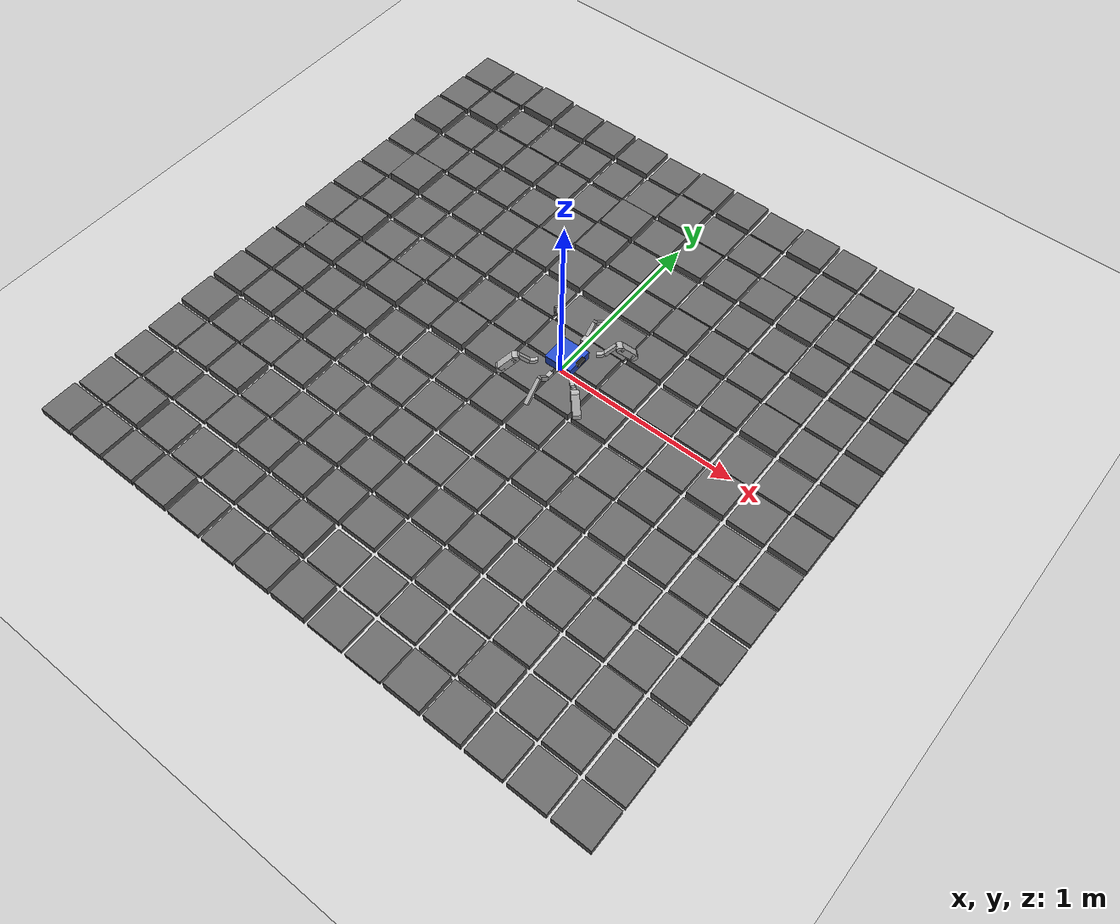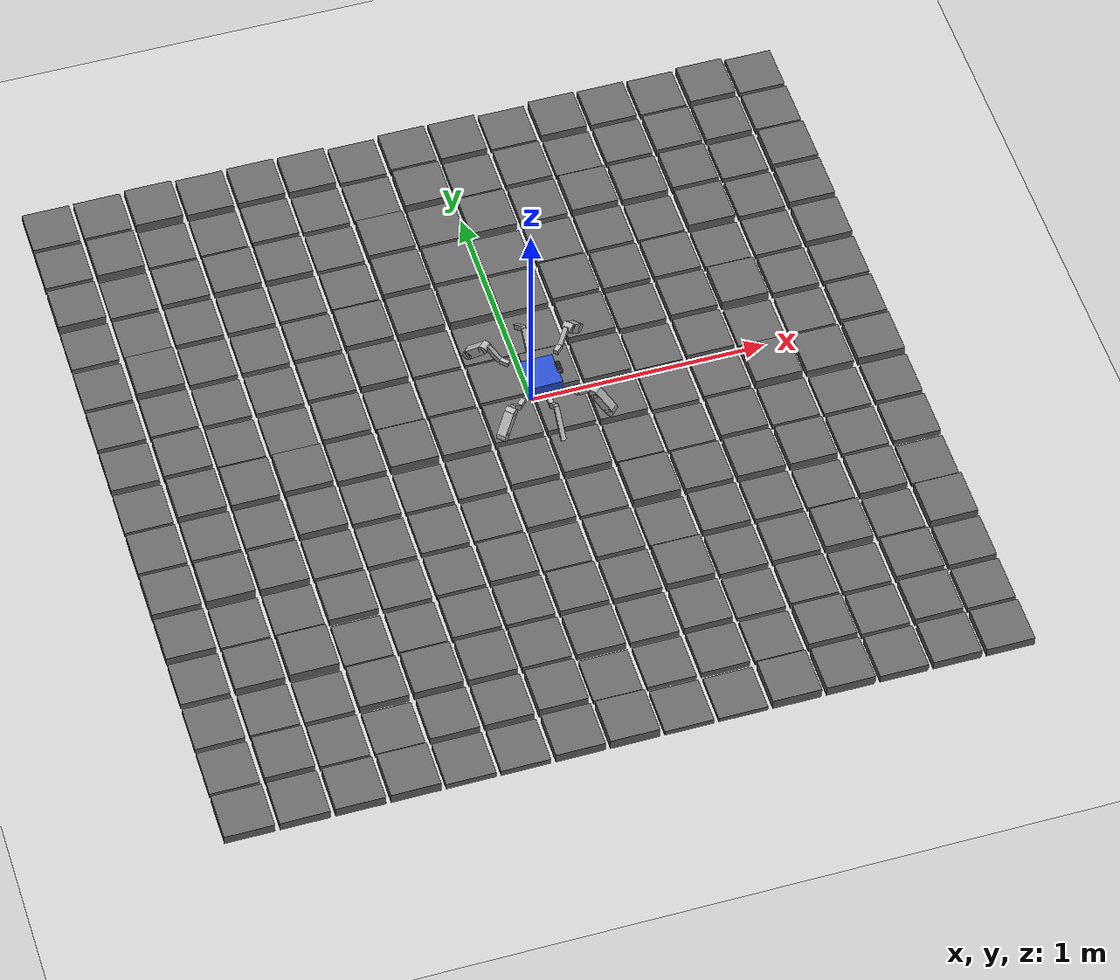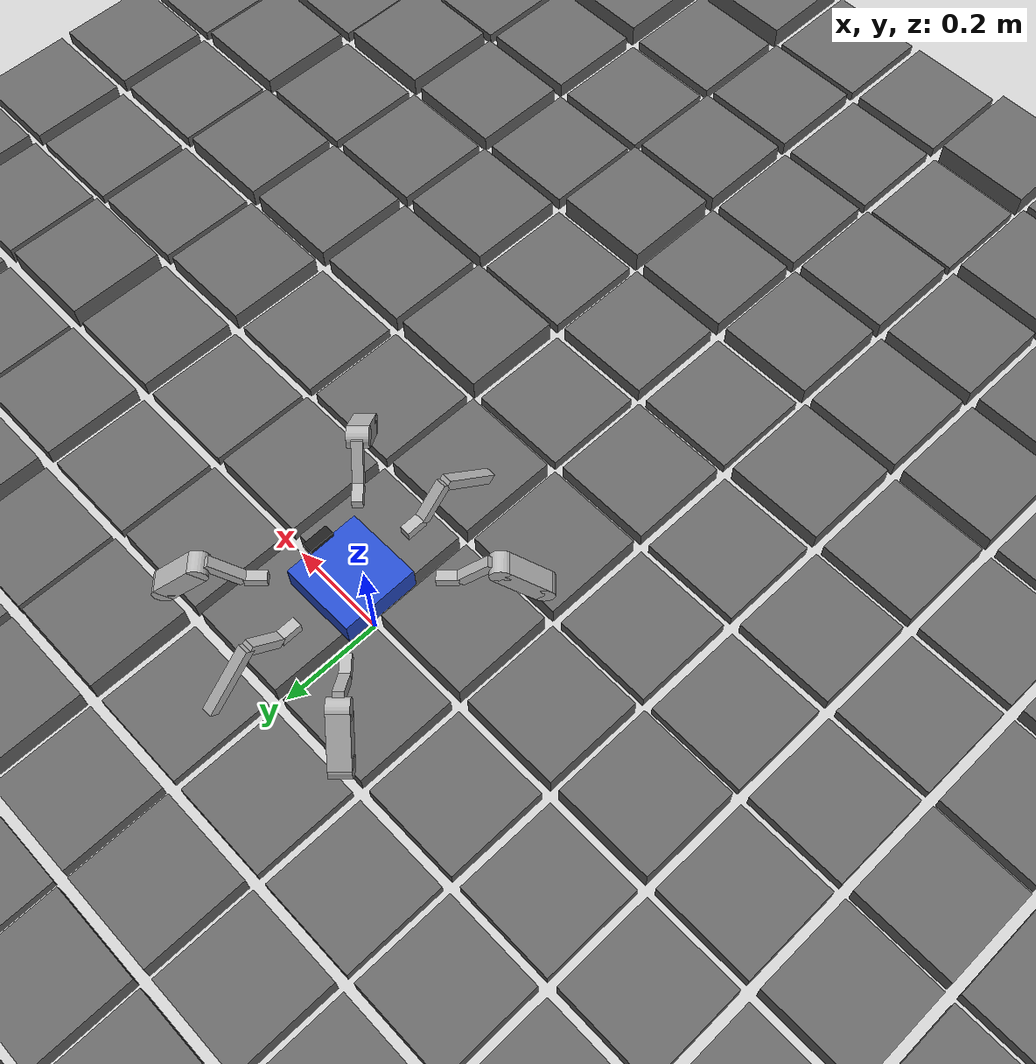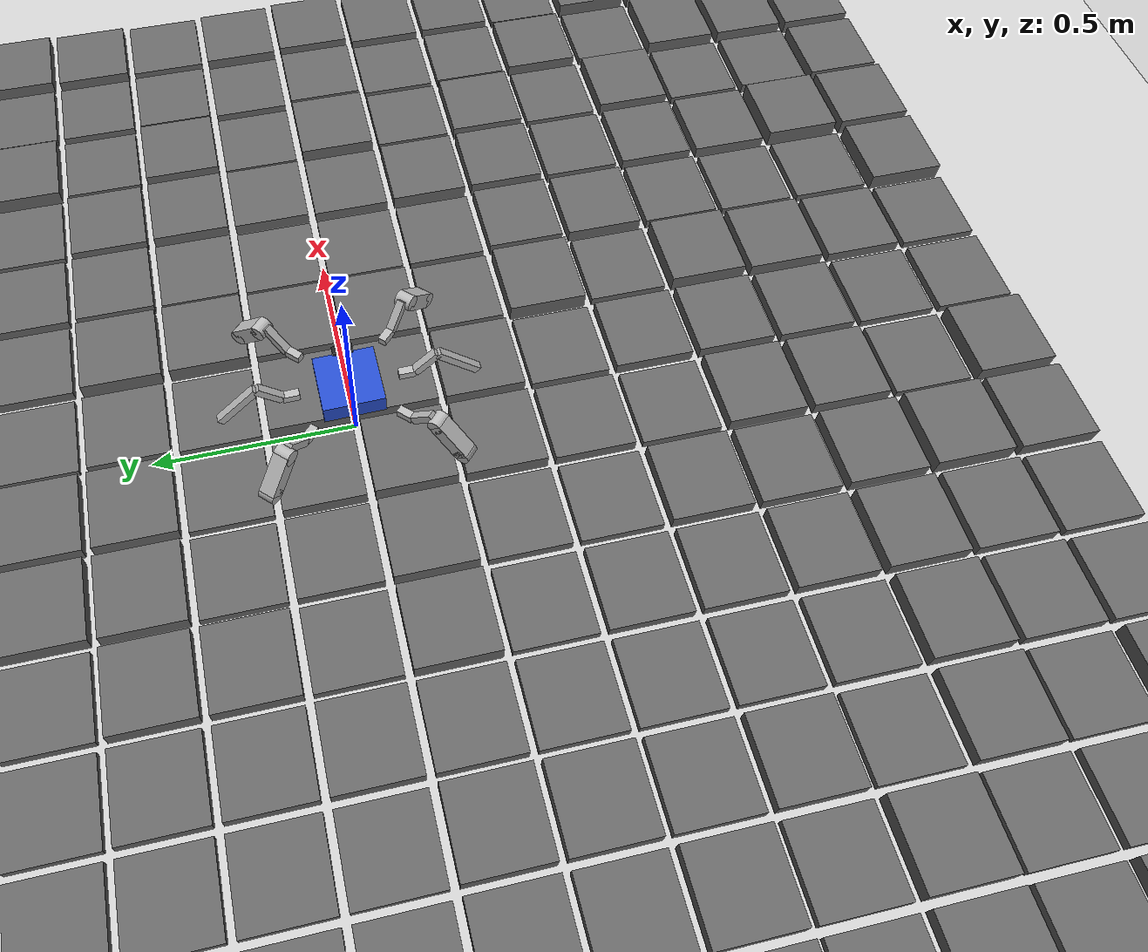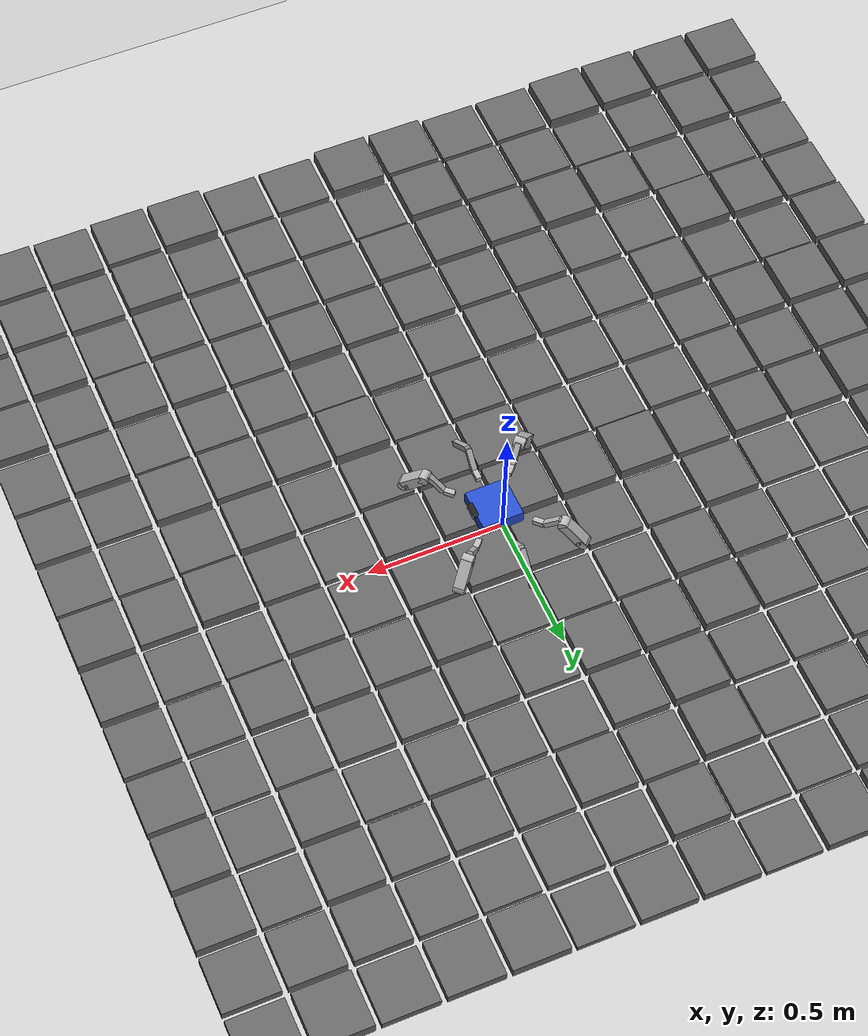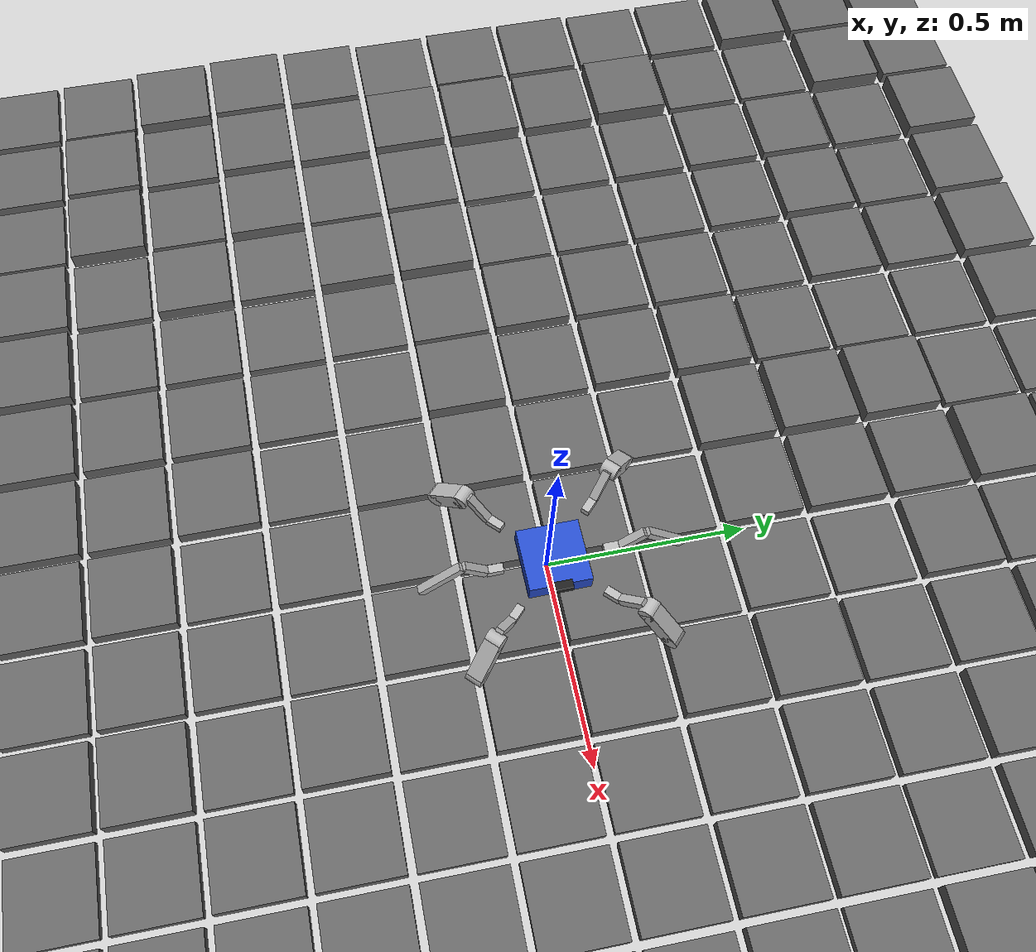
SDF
<sdf version="1.7">
 <world name="default">
  <light name="sun" type="directional">
   <pose>0 0 10 0 -0 0</pose>
   <diffuse>0.8 0.8 0.8 1</diffuse>
   <specular>0.2 0.2 0.2 1</specular>
   <attenuation>
    <range>1000</range>
    <constant>0.9</constant>
    <linear>0.01</linear>
    <quadratic>0.001</quadratic>
   </attenuation>
   <direction>-0.5 0.1 -0.9</direction>
   <spot><inner_angle>0</inner_angle><outer_angle>0</outer_angle><falloff>0</falloff></spot>
  </light>
  <model name="ground_plane">
   <static>1</static>
   <link name="link">
    <collision name="collision">
     <geometry><plane><normal>0 0 1</normal><size>100 100</size></plane></geometry>
     <surface>
      <contact><collide_bitmask>65535</collide_bitmask></contact>
      <friction><ode><mu>100</mu><mu2>50</mu2></ode></friction>
     </surface>
    </collision>
    <visual name="visual">
     <cast_shadows>0</cast_shadows>
     <geometry><plane><normal>0 0 1</normal><size>100 100</size></plane></geometry>
     <material>
      <script><uri>file://media/materials/scripts/gazebo.material</uri><name>Gazebo/Grey</name></script>
     </material>
    </visual>
   </link>
  </model>
  <gravity>0 0 -9.8</gravity>
  <magnetic_field>6e-06 2.3e-05 -4.2e-05</magnetic_field>
  <atmosphere type="adiabatic"/>
  <physics type="ode">
   <max_step_size>0.001</max_step_size>
   <real_time_factor>1</real_time_factor>
   <real_time_update_rate>1000</real_time_update_rate>
  </physics>
  <scene><ambient>0.4 0.4 0.4 1</ambient><background>0.7 0.7 0.7 1</background><shadows>1</shadows></scene>
  <audio><device>default</device></audio>
  <spherical_coordinates>
   <surface_model>EARTH_WGS84</surface_model>
   <latitude_deg>0</latitude_deg>
   <longitude_deg>0</longitude_deg>
   <elevation>0</elevation>
   <heading_deg>0</heading_deg>
  </spherical_coordinates>
  <model name="spider_bot">
   <link name="base_link">
    <inertial>
     <mass>1</mass>
     <inertia><ixx>0.02</ixx><ixy>0</ixy><ixz>0</ixz><iyy>0.02</iyy><iyz>0</iyz><izz>0.04</izz></inertia>
    </inertial>
    <collision name="base_link_collision">
     <geometry><box><size>0.15 0.15 0.05</size></box></geometry>
     <surface><friction><ode><mu>0.2</mu><mu2>0.2</mu2></ode></friction></surface>
    </collision>
    <visual name="base_link_visual">
     <geometry><box><size>0.15 0.15 0.05</size></box></geometry>
     <material>
      <script><name>Gazebo/Blue</name><uri>file://media/materials/scripts/gazebo.material</uri></script>
     </material>
    </visual>
    <visual name="base_link_fixed_joint_lump__camera_link_visual_1">
     <pose>0.08 0 0.025 0 -0 0</pose>
     <geometry><box><size>0.02 0.05 0.02</size></box></geometry>
     <material>
      <script><name>Gazebo/Black</name><uri>file://media/materials/scripts/gazebo.material</uri></script>
     </material>
    </visual>
    <sensor name="depth_camera" type="depth">
     <update_rate>30</update_rate>
     <camera name="head">
      <horizontal_fov>1.39626</horizontal_fov>
      <image><width>640</width><height>480</height><format>R8G8B8</format></image>
      <clip><near>0.05</near><far>3</far></clip>
     </camera>
     <plugin name="camera_controller" filename="libgazebo_ros_camera.so">
      <ros>
       <namespace>/</namespace>
       <remapping>custom_camera/image_raw:=camera/image_raw</remapping>
       <remapping>custom_camera/depth/image_raw:=camera/depth/image_raw</remapping>
      </ros>
      <camera_name>camera</camera_name>
      <frame_name>camera_link</frame_name>
     </plugin>
     <pose>0.08 0 0.025 0 -0 0</pose>
    </sensor>
   </link>
   <joint name="joint1" type="revolute">
    <pose relative_to="base_link">0.1 0.1 0 0 -0 0.785</pose>
    <parent>base_link</parent>
    <child>l1_c</child>
    <axis>
     <xyz>0 0 1</xyz>
     <limit><lower>-1.57</lower><upper>1.57</upper><effort>50</effort><velocity>1</velocity></limit>
     <dynamics>
      <damping>1</damping>
      <friction>0.1</friction>
      <spring_reference>0</spring_reference>
      <spring_stiffness>0</spring_stiffness>
     </dynamics>
    </axis>
   </joint>
   <link name="l1_c">
    <pose relative_to="joint1">0 0 0 0 -0 0</pose>
    <inertial>
     <mass>0.1</mass>
     <inertia><ixx>0.01</ixx><ixy>0</ixy><ixz>0</ixz><iyy>0.01</iyy><iyz>0</iyz><izz>0.01</izz></inertia>
    </inertial>
    <collision name="l1_c_collision">
     <pose>0.02 0 0 0 -0 0</pose>
     <geometry><box><size>0.04 0.02 0.02</size></box></geometry>
    </collision>
    <visual name="l1_c_visual">
     <pose>0.02 0 0 0 -0 0</pose>
     <geometry><box><size>0.04 0.02 0.02</size></box></geometry>
    </visual>
   </link>
   <joint name="joint2" type="revolute">
    <pose relative_to="l1_c">0.04 0 0 0 -0.785 0</pose>
    <parent>l1_c</parent>
    <child>l1_f</child>
    <axis>
     <xyz>0 -1 0</xyz>
     <limit><lower>-3.14</lower><upper>3.14</upper><effort>50</effort><velocity>1</velocity></limit>
     <dynamics>
      <damping>1</damping>
      <friction>0.1</friction>
      <spring_reference>0</spring_reference>
      <spring_stiffness>0</spring_stiffness>
     </dynamics>
    </axis>
   </joint>
   <link name="l1_f">
    <pose relative_to="joint2">0 0 0 0 -0 0</pose>
    <inertial>
     <mass>0.1</mass>
     <inertia><ixx>0.01</ixx><ixy>0</ixy><ixz>0</ixz><iyy>0.01</iyy><iyz>0</iyz><izz>0.01</izz></inertia>
    </inertial>
    <collision name="l1_f_collision">
     <pose>0.04 0 0 0 -0 0</pose>
     <geometry><box><size>0.08 0.02 0.02</size></box></geometry>
    </collision>
    <visual name="l1_f_visual">
     <pose>0.04 0 0 0 -0 0</pose>
     <geometry><box><size>0.08 0.02 0.02</size></box></geometry>
    </visual>
   </link>
   <joint name="joint3" type="revolute">
    <pose relative_to="l1_f">0.08 0 0 0 1.57 0</pose>
    <parent>l1_f</parent>
    <child>l1_t</child>
    <axis>
     <xyz>0 -1 0</xyz>
     <limit><lower>-3.14</lower><upper>3.14</upper><effort>50</effort><velocity>1</velocity></limit>
     <dynamics>
      <damping>1</damping>
      <friction>0.1</friction>
      <spring_reference>0</spring_reference>
      <spring_stiffness>0</spring_stiffness>
     </dynamics>
    </axis>
   </joint>
   <link name="l1_t">
    <pose relative_to="joint3">0 0 0 0 -0 0</pose>
    <inertial>
     <mass>0.1</mass>
     <inertia><ixx>0.001</ixx><ixy>0</ixy><ixz>0</ixz><iyy>0.001</iyy><iyz>0</iyz><izz>0.001</izz></inertia>
    </inertial>
    <collision name="l1_t_collision">
     <pose>0.07 0 0 0 -0 0</pose>
     <geometry><box><size>0.14 0.04 0.04</size></box></geometry>
     <surface>
      <contact><ode><kp>10000</kp><kd>100</kd></ode></contact>
      <friction><ode><mu>8</mu><mu2>8</mu2></ode></friction>
     </surface>
    </collision>
    <visual name="l1_t_visual">
     <pose>0.07 0 0 0 -0 0</pose>
     <geometry><box><size>0.1 0.04 0.04</size></box></geometry>
    </visual>
    <visual name="l1_t_visual_1">
     <pose>0.02 0 0 1.5708 -0 0</pose>
     <geometry><cylinder><length>0.04</length><radius>0.02</radius></cylinder></geometry>
    </visual>
    <visual name="l1_t_visual_2">
     <pose>0.12 0 0 1.5708 -0 0</pose>
     <geometry><cylinder><length>0.04</length><radius>0.02</radius></cylinder></geometry>
    </visual>
    <self_collide>1</self_collide>
   </link>
   <joint name="joint10" type="revolute">
    <pose relative_to="base_link">-0.1 -0.1 0 0 0 -2.355</pose>
    <parent>base_link</parent>
    <child>l4_c</child>
    <axis>
     <xyz>0 0 1</xyz>
     <limit><lower>-1.57</lower><upper>1.57</upper><effort>50</effort><velocity>1</velocity></limit>
     <dynamics>
      <damping>1</damping>
      <friction>0.1</friction>
      <spring_reference>0</spring_reference>
      <spring_stiffness>0</spring_stiffness>
     </dynamics>
    </axis>
   </joint>
   <link name="l4_c">
    <pose relative_to="joint10">0 0 0 0 -0 0</pose>
    <inertial>
     <mass>0.1</mass>
     <inertia><ixx>0.01</ixx><ixy>0</ixy><ixz>0</ixz><iyy>0.01</iyy><iyz>0</iyz><izz>0.01</izz></inertia>
    </inertial>
    <collision name="l4_c_collision">
     <pose>0.02 0 0 0 -0 0</pose>
     <geometry><box><size>0.04 0.02 0.02</size></box></geometry>
    </collision>
    <visual name="l4_c_visual">
     <pose>0.02 0 0 0 -0 0</pose>
     <geometry><box><size>0.04 0.02 0.02</size></box></geometry>
    </visual>
   </link>
   <joint name="joint11" type="revolute">
    <pose relative_to="l4_c">0.04 0 0 0 -0.785 0</pose>
    <parent>l4_c</parent>
    <child>l4_f</child>
    <axis>
     <xyz>0 -1 0</xyz>
     <limit><lower>-3.14</lower><upper>3.14</upper><effort>50</effort><velocity>1</velocity></limit>
     <dynamics>
      <damping>1</damping>
      <friction>0.1</friction>
      <spring_reference>0</spring_reference>
      <spring_stiffness>0</spring_stiffness>
     </dynamics>
    </axis>
   </joint>
   <link name="l4_f">
    <pose relative_to="joint11">0 0 0 0 -0 0</pose>
    <inertial>
     <mass>0.1</mass>
     <inertia><ixx>0.01</ixx><ixy>0</ixy><ixz>0</ixz><iyy>0.01</iyy><iyz>0</iyz><izz>0.01</izz></inertia>
    </inertial>
    <collision name="l4_f_collision">
     <pose>0.04 0 0 0 -0 0</pose>
     <geometry><box><size>0.08 0.02 0.02</size></box></geometry>
    </collision>
    <visual name="l4_f_visual">
     <pose>0.04 0 0 0 -0 0</pose>
     <geometry><box><size>0.08 0.02 0.02</size></box></geometry>
    </visual>
   </link>
   <joint name="joint12" type="revolute">
    <pose relative_to="l4_f">0.08 0 0 0 1.57 0</pose>
    <parent>l4_f</parent>
    <child>l4_t</child>
    <axis>
     <xyz>0 -1 0</xyz>
     <limit><lower>-3.14</lower><upper>3.14</upper><effort>50</effort><velocity>1</velocity></limit>
     <dynamics>
      <damping>1</damping>
      <friction>0.1</friction>
      <spring_reference>0</spring_reference>
      <spring_stiffness>0</spring_stiffness>
     </dynamics>
    </axis>
   </joint>
   <link name="l4_t">
    <pose relative_to="joint12">0 0 0 0 -0 0</pose>
    <inertial>
     <mass>0.1</mass>
     <inertia><ixx>0.001</ixx><ixy>0</ixy><ixz>0</ixz><iyy>0.001</iyy><iyz>0</iyz><izz>0.001</izz></inertia>
    </inertial>
    <collision name="l4_t_collision">
     <pose>0.07 0 0 0 -0 0</pose>
     <geometry><box><size>0.14 0.04 0.04</size></box></geometry>
     <surface>
      <contact><ode><kp>10000</kp><kd>100</kd></ode></contact>
      <friction><ode><mu>8</mu><mu2>8</mu2></ode></friction>
     </surface>
    </collision>
    <visual name="l4_t_visual">
     <pose>0.07 0 0 0 -0 0</pose>
     <geometry><box><size>0.1 0.04 0.04</size></box></geometry>
    </visual>
    <visual name="l4_t_visual_1">
     <pose>0.02 0 0 1.5708 -0 0</pose>
     <geometry><cylinder><length>0.04</length><radius>0.02</radius></cylinder></geometry>
    </visual>
    <visual name="l4_t_visual_2">
     <pose>0.12 0 0 1.5708 -0 0</pose>
     <geometry><cylinder><length>0.04</length><radius>0.02</radius></cylinder></geometry>
    </visual>
    <self_collide>1</self_collide>
   </link>
   <joint name="joint13" type="revolute">
    <pose relative_to="base_link">0 -0.12 0 0 0 -1.57</pose>
    <parent>base_link</parent>
    <child>l5_c</child>
    <axis>
     <xyz>0 0 1</xyz>
     <limit><lower>-1.57</lower><upper>1.57</upper><effort>50</effort><velocity>1</velocity></limit>
     <dynamics>
      <damping>1</damping>
      <friction>0.1</friction>
      <spring_reference>0</spring_reference>
      <spring_stiffness>0</spring_stiffness>
     </dynamics>
    </axis>
   </joint>
   <link name="l5_c">
    <pose relative_to="joint13">0 0 0 0 -0 0</pose>
    <inertial>
     <mass>0.1</mass>
     <inertia><ixx>0.01</ixx><ixy>0</ixy><ixz>0</ixz><iyy>0.01</iyy><iyz>0</iyz><izz>0.01</izz></inertia>
    </inertial>
    <collision name="l5_c_collision">
     <pose>0.02 0 0 0 -0 0</pose>
     <geometry><box><size>0.04 0.02 0.02</size></box></geometry>
    </collision>
    <visual name="l5_c_visual">
     <pose>0.02 0 0 0 -0 0</pose>
     <geometry><box><size>0.04 0.02 0.02</size></box></geometry>
    </visual>
   </link>
   <joint name="joint14" type="revolute">
    <pose relative_to="l5_c">0.04 0 0 0 -0.785 0</pose>
    <parent>l5_c</parent>
    <child>l5_f</child>
    <axis>
     <xyz>0 -1 0</xyz>
     <limit><lower>-3.14</lower><upper>3.14</upper><effort>50</effort><velocity>1</velocity></limit>
     <dynamics>
      <damping>1</damping>
      <friction>0.1</friction>
      <spring_reference>0</spring_reference>
      <spring_stiffness>0</spring_stiffness>
     </dynamics>
    </axis>
   </joint>
   <link name="l5_f">
    <pose relative_to="joint14">0 0 0 0 -0 0</pose>
    <inertial>
     <mass>0.1</mass>
     <inertia><ixx>0.01</ixx><ixy>0</ixy><ixz>0</ixz><iyy>0.01</iyy><iyz>0</iyz><izz>0.01</izz></inertia>
    </inertial>
    <collision name="l5_f_collision">
     <pose>0.04 0 0 0 -0 0</pose>
     <geometry><box><size>0.08 0.02 0.02</size></box></geometry>
    </collision>
    <visual name="l5_f_visual">
     <pose>0.04 0 0 0 -0 0</pose>
     <geometry><box><size>0.08 0.02 0.02</size></box></geometry>
    </visual>
   </link>
   <joint name="joint15" type="revolute">
    <pose relative_to="l5_f">0.08 0 0 0 1.57 0</pose>
    <parent>l5_f</parent>
    <child>l5_t</child>
    <axis>
     <xyz>0 -1 0</xyz>
     <limit><lower>-3.14</lower><upper>3.14</upper><effort>50</effort><velocity>1</velocity></limit>
     <dynamics>
      <damping>1</damping>
      <friction>0.1</friction>
      <spring_reference>0</spring_reference>
      <spring_stiffness>0</spring_stiffness>
     </dynamics>
    </axis>
   </joint>
   <link name="l5_t">
    <pose relative_to="joint15">0 0 0 0 -0 0</pose>
    <inertial>
     <mass>0.1</mass>
     <inertia><ixx>0.01</ixx><ixy>0</ixy><ixz>0</ixz><iyy>0.01</iyy><iyz>0</iyz><izz>0.01</izz></inertia>
    </inertial>
    <collision name="l5_t_collision">
     <pose>0.07 0 0 0 -0 0</pose>
     <geometry><box><size>0.14 0.02 0.02</size></box></geometry>
     <surface>
      <contact><ode><kp>10000</kp><kd>100</kd></ode></contact>
      <friction><ode><mu>8</mu><mu2>8</mu2></ode></friction>
     </surface>
    </collision>
    <visual name="l5_t_visual">
     <pose>0.07 0 0 0 -0 0</pose>
     <geometry><box><size>0.14 0.02 0.02</size></box></geometry>
    </visual>
    <self_collide>1</self_collide>
   </link>
   <joint name="joint16" type="revolute">
    <pose relative_to="base_link">0.1 -0.1 0 0 0 -0.785</pose>
    <parent>base_link</parent>
    <child>l6_c</child>
    <axis>
     <xyz>0 0 1</xyz>
     <limit><lower>-1.57</lower><upper>1.57</upper><effort>50</effort><velocity>1</velocity></limit>
     <dynamics>
      <damping>1</damping>
      <friction>0.1</friction>
      <spring_reference>0</spring_reference>
      <spring_stiffness>0</spring_stiffness>
     </dynamics>
    </axis>
   </joint>
   <link name="l6_c">
    <pose relative_to="joint16">0 0 0 0 -0 0</pose>
    <inertial>
     <mass>0.1</mass>
     <inertia><ixx>0.01</ixx><ixy>0</ixy><ixz>0</ixz><iyy>0.01</iyy><iyz>0</iyz><izz>0.01</izz></inertia>
    </inertial>
    <collision name="l6_c_collision">
     <pose>0.02 0 0 0 -0 0</pose>
     <geometry><box><size>0.04 0.02 0.02</size></box></geometry>
    </collision>
    <visual name="l6_c_visual">
     <pose>0.02 0 0 0 -0 0</pose>
     <geometry><box><size>0.04 0.02 0.02</size></box></geometry>
    </visual>
   </link>
   <joint name="joint17" type="revolute">
    <pose relative_to="l6_c">0.04 0 0 0 -0.785 0</pose>
    <parent>l6_c</parent>
    <child>l6_f</child>
    <axis>
     <xyz>0 -1 0</xyz>
     <limit><lower>-3.14</lower><upper>3.14</upper><effort>50</effort><velocity>1</velocity></limit>
     <dynamics>
      <damping>1</damping>
      <friction>0.1</friction>
      <spring_reference>0</spring_reference>
      <spring_stiffness>0</spring_stiffness>
     </dynamics>
    </axis>
   </joint>
   <link name="l6_f">
    <pose relative_to="joint17">0 0 0 0 -0 0</pose>
    <inertial>
     <mass>0.1</mass>
     <inertia><ixx>0.01</ixx><ixy>0</ixy><ixz>0</ixz><iyy>0.01</iyy><iyz>0</iyz><izz>0.01</izz></inertia>
    </inertial>
    <collision name="l6_f_collision">
     <pose>0.04 0 0 0 -0 0</pose>
     <geometry><box><size>0.08 0.02 0.02</size></box></geometry>
    </collision>
    <visual name="l6_f_visual">
     <pose>0.04 0 0 0 -0 0</pose>
     <geometry><box><size>0.08 0.02 0.02</size></box></geometry>
    </visual>
   </link>
   <joint name="joint18" type="revolute">
    <pose relative_to="l6_f">0.08 0 0 0 1.57 0</pose>
    <parent>l6_f</parent>
    <child>l6_t</child>
    <axis>
     <xyz>0 -1 0</xyz>
     <limit><lower>-3.14</lower><upper>3.14</upper><effort>50</effort><velocity>1</velocity></limit>
     <dynamics>
      <damping>1</damping>
      <friction>0.1</friction>
      <spring_reference>0</spring_reference>
      <spring_stiffness>0</spring_stiffness>
     </dynamics>
    </axis>
   </joint>
   <link name="l6_t">
    <pose relative_to="joint18">0 0 0 0 -0 0</pose>
    <inertial>
     <mass>0.1</mass>
     <inertia><ixx>0.001</ixx><ixy>0</ixy><ixz>0</ixz><iyy>0.001</iyy><iyz>0</iyz><izz>0.001</izz></inertia>
    </inertial>
    <collision name="l6_t_collision">
     <pose>0.07 0 0 0 -0 0</pose>
     <geometry><box><size>0.14 0.04 0.04</size></box></geometry>
     <surface>
      <contact><ode><kp>10000</kp><kd>100</kd></ode></contact>
      <friction><ode><mu>8</mu><mu2>8</mu2></ode></friction>
     </surface>
    </collision>
    <visual name="l6_t_visual">
     <pose>0.07 0 0 0 -0 0</pose>
     <geometry><box><size>0.1 0.04 0.04</size></box></geometry>
    </visual>
    <visual name="l6_t_visual_1">
     <pose>0.02 0 0 1.5708 -0 0</pose>
     <geometry><cylinder><length>0.04</length><radius>0.02</radius></cylinder></geometry>
    </visual>
    <visual name="l6_t_visual_2">
     <pose>0.12 0 0 1.5708 -0 0</pose>
     <geometry><cylinder><length>0.04</length><radius>0.02</radius></cylinder></geometry>
    </visual>
    <self_collide>1</self_collide>
   </link>
   <joint name="joint4" type="revolute">
    <pose relative_to="base_link">0 0.12 0 0 -0 1.57</pose>
    <parent>base_link</parent>
    <child>l2_c</child>
    <axis>
     <xyz>0 0 1</xyz>
     <limit><lower>-1.57</lower><upper>1.57</upper><effort>50</effort><velocity>1</velocity></limit>
     <dynamics>
      <damping>1</damping>
      <friction>0.1</friction>
      <spring_reference>0</spring_reference>
      <spring_stiffness>0</spring_stiffness>
     </dynamics>
    </axis>
   </joint>
   <link name="l2_c">
    <pose relative_to="joint4">0 0 0 0 -0 0</pose>
    <inertial>
     <mass>0.1</mass>
     <inertia><ixx>0.01</ixx><ixy>0</ixy><ixz>0</ixz><iyy>0.01</iyy><iyz>0</iyz><izz>0.01</izz></inertia>
    </inertial>
    <collision name="l2_c_collision">
     <pose>0.02 0 0 0 -0 0</pose>
     <geometry><box><size>0.04 0.02 0.02</size></box></geometry>
    </collision>
    <visual name="l2_c_visual">
     <pose>0.02 0 0 0 -0 0</pose>
     <geometry><box><size>0.04 0.02 0.02</size></box></geometry>
    </visual>
   </link>
   <joint name="joint5" type="revolute">
    <pose relative_to="l2_c">0.04 0 0 0 -0.785 0</pose>
    <parent>l2_c</parent>
    <child>l2_f</child>
    <axis>
     <xyz>0 -1 0</xyz>
     <limit><lower>-3.14</lower><upper>3.14</upper><effort>50</effort><velocity>1</velocity></limit>
     <dynamics>
      <damping>1</damping>
      <friction>0.1</friction>
      <spring_reference>0</spring_reference>
      <spring_stiffness>0</spring_stiffness>
     </dynamics>
    </axis>
   </joint>
   <link name="l2_f">
    <pose relative_to="joint5">0 0 0 0 -0 0</pose>
    <inertial>
     <mass>0.1</mass>
     <inertia><ixx>0.01</ixx><ixy>0</ixy><ixz>0</ixz><iyy>0.01</iyy><iyz>0</iyz><izz>0.01</izz></inertia>
    </inertial>
    <collision name="l2_f_collision">
     <pose>0.04 0 0 0 -0 0</pose>
     <geometry><box><size>0.08 0.02 0.02</size></box></geometry>
    </collision>
    <visual name="l2_f_visual">
     <pose>0.04 0 0 0 -0 0</pose>
     <geometry><box><size>0.08 0.02 0.02</size></box></geometry>
    </visual>
   </link>
   <joint name="joint6" type="revolute">
    <pose relative_to="l2_f">0.08 0 0 0 1.57 0</pose>
    <parent>l2_f</parent>
    <child>l2_t</child>
    <axis>
     <xyz>0 -1 0</xyz>
     <limit><lower>-3.14</lower><upper>3.14</upper><effort>50</effort><velocity>1</velocity></limit>
     <dynamics>
      <damping>1</damping>
      <friction>0.1</friction>
      <spring_reference>0</spring_reference>
      <spring_stiffness>0</spring_stiffness>
     </dynamics>
    </axis>
   </joint>
   <link name="l2_t">
    <pose relative_to="joint6">0 0 0 0 -0 0</pose>
    <inertial>
     <mass>0.1</mass>
     <inertia><ixx>0.01</ixx><ixy>0</ixy><ixz>0</ixz><iyy>0.01</iyy><iyz>0</iyz><izz>0.01</izz></inertia>
    </inertial>
    <collision name="l2_t_collision">
     <pose>0.07 0 0 0 -0 0</pose>
     <geometry><box><size>0.14 0.02 0.02</size></box></geometry>
     <surface>
      <contact><ode><kp>10000</kp><kd>100</kd></ode></contact>
      <friction><ode><mu>8</mu><mu2>8</mu2></ode></friction>
     </surface>
    </collision>
    <visual name="l2_t_visual">
     <pose>0.07 0 0 0 -0 0</pose>
     <geometry><box><size>0.14 0.02 0.02</size></box></geometry>
    </visual>
    <self_collide>1</self_collide>
   </link>
   <joint name="joint7" type="revolute">
    <pose relative_to="base_link">-0.1 0.1 0 0 -0 2.355</pose>
    <parent>base_link</parent>
    <child>l3_c</child>
    <axis>
     <xyz>0 0 1</xyz>
     <limit><lower>-1.57</lower><upper>1.57</upper><effort>50</effort><velocity>1</velocity></limit>
     <dynamics>
      <damping>1</damping>
      <friction>0.1</friction>
      <spring_reference>0</spring_reference>
      <spring_stiffness>0</spring_stiffness>
     </dynamics>
    </axis>
   </joint>
   <link name="l3_c">
    <pose relative_to="joint7">0 0 0 0 -0 0</pose>
    <inertial>
     <mass>0.1</mass>
     <inertia><ixx>0.01</ixx><ixy>0</ixy><ixz>0</ixz><iyy>0.01</iyy><iyz>0</iyz><izz>0.01</izz></inertia>
    </inertial>
    <collision name="l3_c_collision">
     <pose>0.02 0 0 0 -0 0</pose>
     <geometry><box><size>0.04 0.02 0.02</size></box></geometry>
    </collision>
    <visual name="l3_c_visual">
     <pose>0.02 0 0 0 -0 0</pose>
     <geometry><box><size>0.04 0.02 0.02</size></box></geometry>
    </visual>
   </link>
   <joint name="joint8" type="revolute">
    <pose relative_to="l3_c">0.04 0 0 0 -0.785 0</pose>
    <parent>l3_c</parent>
    <child>l3_f</child>
    <axis>
     <xyz>0 -1 0</xyz>
     <limit><lower>-3.14</lower><upper>3.14</upper><effort>50</effort><velocity>1</velocity></limit>
     <dynamics>
      <damping>1</damping>
      <friction>0.1</friction>
      <spring_reference>0</spring_reference>
      <spring_stiffness>0</spring_stiffness>
     </dynamics>
    </axis>
   </joint>
   <link name="l3_f">
    <pose relative_to="joint8">0 0 0 0 -0 0</pose>
    <inertial>
     <mass>0.1</mass>
     <inertia><ixx>0.01</ixx><ixy>0</ixy><ixz>0</ixz><iyy>0.01</iyy><iyz>0</iyz><izz>0.01</izz></inertia>
    </inertial>
    <collision name="l3_f_collision">
     <pose>0.04 0 0 0 -0 0</pose>
     <geometry><box><size>0.08 0.02 0.02</size></box></geometry>
    </collision>
    <visual name="l3_f_visual">
     <pose>0.04 0 0 0 -0 0</pose>
     <geometry><box><size>0.08 0.02 0.02</size></box></geometry>
    </visual>
   </link>
   <joint name="joint9" type="revolute">
    <pose relative_to="l3_f">0.08 0 0 0 1.57 0</pose>
    <parent>l3_f</parent>
    <child>l3_t</child>
    <axis>
     <xyz>0 -1 0</xyz>
     <limit><lower>-3.14</lower><upper>3.14</upper><effort>50</effort><velocity>1</velocity></limit>
     <dynamics>
      <damping>1</damping>
      <friction>0.1</friction>
      <spring_reference>0</spring_reference>
      <spring_stiffness>0</spring_stiffness>
     </dynamics>
    </axis>
   </joint>
   <link name="l3_t">
    <pose relative_to="joint9">0 0 0 0 -0 0</pose>
    <inertial>
     <mass>0.1</mass>
     <inertia><ixx>0.001</ixx><ixy>0</ixy><ixz>0</ixz><iyy>0.001</iyy><iyz>0</iyz><izz>0.001</izz></inertia>
    </inertial>
    <collision name="l3_t_collision">
     <pose>0.07 0 0 0 -0 0</pose>
     <geometry><box><size>0.14 0.04 0.04</size></box></geometry>
     <surface>
      <contact><ode><kp>10000</kp><kd>100</kd></ode></contact>
      <friction><ode><mu>8</mu><mu2>8</mu2></ode></friction>
     </surface>
    </collision>
    <visual name="l3_t_visual">
     <pose>0.07 0 0 0 -0 0</pose>
     <geometry><box><size>0.1 0.04 0.04</size></box></geometry>
    </visual>
    <visual name="l3_t_visual_1">
     <pose>0.02 0 0 1.5708 -0 0</pose>
     <geometry><cylinder><length>0.04</length><radius>0.02</radius></cylinder></geometry>
    </visual>
    <visual name="l3_t_visual_2">
     <pose>0.12 0 0 1.5708 -0 0</pose>
     <geometry><cylinder><length>0.04</length><radius>0.02</radius></cylinder></geometry>
    </visual>
    <self_collide>1</self_collide>
   </link>
   <static>0</static>
   <plugin name="gazebo_ros2_control" filename="libgazebo_ros2_control.so">
    <parameters>/home/chia/spider_ws/install/spider_bot/share/spider_bot/config/spider_bot_controllers.yaml</parameters>
   </plugin>
   <plugin name="gazebo_ros_p3d" filename="libgazebo_ros_p3d.so">
    <ros><namespace>/</namespace><remapping>odom:=odom</remapping></ros>
    <body_name>base_link</body_name>
    <frame_name>world</frame_name>
    <update_rate>50</update_rate>
   </plugin>
   <pose>0.037872 0.001576 0.137081 -0.010307 -0.001623 0.012647</pose>
  </model>
  <model name="terrain_0_0">
   <static>1</static>
   <link name="link">
    <collision name="collision">
     <geometry><box><size>0.2 0.2 0.041049</size></box></geometry>
     <surface><friction><ode><mu>100</mu><mu2>100</mu2></ode></friction></surface>
    </collision>
    <visual name="visual">
     <geometry><box><size>0.2 0.2 0.041049</size></box></geometry>
     <material><ambient>0.4 0.4 0.4 1</ambient></material>
    </visual>
   </link>
   <pose>-1.65 -1.65 0.020525 0 -0 0</pose>
  </model>
  <model name="terrain_0_1">
   <static>1</static>
   <link name="link">
    <collision name="collision">
     <geometry><box><size>0.2 0.2 0.025802</size></box></geometry>
     <surface><friction><ode><mu>100</mu><mu2>100</mu2></ode></friction></surface>
    </collision>
    <visual name="visual">
     <geometry><box><size>0.2 0.2 0.025802</size></box></geometry>
     <material><ambient>0.4 0.4 0.4 1</ambient></material>
    </visual>
   </link>
   <pose>-1.65 -1.43 0.012901 0 -0 0</pose>
  </model>
  <model name="terrain_0_2">
   <static>1</static>
   <link name="link">
    <collision name="collision">
     <geometry><box><size>0.2 0.2 0.024704</size></box></geometry>
     <surface><friction><ode><mu>100</mu><mu2>100</mu2></ode></friction></surface>
    </collision>
    <visual name="visual">
     <geometry><box><size>0.2 0.2 0.024704</size></box></geometry>
     <material><ambient>0.4 0.4 0.4 1</ambient></material>
    </visual>
   </link>
   <pose>-1.65 -1.21 0.012352 0 -0 0</pose>
  </model>
  <model name="terrain_0_3">
   <static>1</static>
   <link name="link">
    <collision name="collision">
     <geometry><box><size>0.2 0.2 0.028086</size></box></geometry>
     <surface><friction><ode><mu>100</mu><mu2>100</mu2></ode></friction></surface>
    </collision>
    <visual name="visual">
     <geometry><box><size>0.2 0.2 0.028086</size></box></geometry>
     <material><ambient>0.4 0.4 0.4 1</ambient></material>
    </visual>
   </link>
   <pose>-1.65 -0.99 0.014043 0 -0 0</pose>
  </model>
  <model name="terrain_0_4">
   <static>1</static>
   <link name="link">
    <collision name="collision">
     <geometry><box><size>0.2 0.2 0.040163</size></box></geometry>
     <surface><friction><ode><mu>100</mu><mu2>100</mu2></ode></friction></surface>
    </collision>
    <visual name="visual">
     <geometry><box><size>0.2 0.2 0.040163</size></box></geometry>
     <material><ambient>0.4 0.4 0.4 1</ambient></material>
    </visual>
   </link>
   <pose>-1.65 -0.77 0.020081 0 -0 0</pose>
  </model>
  <model name="terrain_0_5">
   <static>1</static>
   <link name="link">
    <collision name="collision">
     <geometry><box><size>0.2 0.2 0.045397</size></box></geometry>
     <surface><friction><ode><mu>100</mu><mu2>100</mu2></ode></friction></surface>
    </collision>
    <visual name="visual">
     <geometry><box><size>0.2 0.2 0.045397</size></box></geometry>
     <material><ambient>0.4 0.4 0.4 1</ambient></material>
    </visual>
   </link>
   <pose>-1.65 -0.55 0.022699 0 -0 0</pose>
  </model>
  <model name="terrain_0_6">
   <static>1</static>
   <link name="link">
    <collision name="collision">
     <geometry><box><size>0.2 0.2 0.035923</size></box></geometry>
     <surface><friction><ode><mu>100</mu><mu2>100</mu2></ode></friction></surface>
    </collision>
    <visual name="visual">
     <geometry><box><size>0.2 0.2 0.035923</size></box></geometry>
     <material><ambient>0.4 0.4 0.4 1</ambient></material>
    </visual>
   </link>
   <pose>-1.65 -0.33 0.017961 0 -0 0</pose>
  </model>
  <model name="terrain_0_7">
   <static>1</static>
   <link name="link">
    <collision name="collision">
     <geometry><box><size>0.2 0.2 0.023461</size></box></geometry>
     <surface><friction><ode><mu>100</mu><mu2>100</mu2></ode></friction></surface>
    </collision>
    <visual name="visual">
     <geometry><box><size>0.2 0.2 0.023461</size></box></geometry>
     <material><ambient>0.4 0.4 0.4 1</ambient></material>
    </visual>
   </link>
   <pose>-1.65 -0.11 0.011731 0 -0 0</pose>
  </model>
  <model name="terrain_0_8">
   <static>1</static>
   <link name="link">
    <collision name="collision">
     <geometry><box><size>0.2 0.2 0.029653</size></box></geometry>
     <surface><friction><ode><mu>100</mu><mu2>100</mu2></ode></friction></surface>
    </collision>
    <visual name="visual">
     <geometry><box><size>0.2 0.2 0.029653</size></box></geometry>
     <material><ambient>0.4 0.4 0.4 1</ambient></material>
    </visual>
   </link>
   <pose>-1.65 0.11 0.014827 0 -0 0</pose>
  </model>
  <model name="terrain_0_9">
   <static>1</static>
   <link name="link">
    <collision name="collision">
     <geometry><box><size>0.2 0.2 0.027519</size></box></geometry>
     <surface><friction><ode><mu>100</mu><mu2>100</mu2></ode></friction></surface>
    </collision>
    <visual name="visual">
     <geometry><box><size>0.2 0.2 0.027519</size></box></geometry>
     <material><ambient>0.4 0.4 0.4 1</ambient></material>
    </visual>
   </link>
   <pose>-1.65 0.33 0.013759 0 -0 0</pose>
  </model>
  <model name="terrain_0_10">
   <static>1</static>
   <link name="link">
    <collision name="collision">
     <geometry><box><size>0.2 0.2 0.021272</size></box></geometry>
     <surface><friction><ode><mu>100</mu><mu2>100</mu2></ode></friction></surface>
    </collision>
    <visual name="visual">
     <geometry><box><size>0.2 0.2 0.021272</size></box></geometry>
     <material><ambient>0.4 0.4 0.4 1</ambient></material>
    </visual>
   </link>
   <pose>-1.65 0.55 0.010636 0 -0 0</pose>
  </model>
  <model name="terrain_0_11">
   <static>1</static>
   <link name="link">
    <collision name="collision">
     <geometry><box><size>0.2 0.2 0.022224</size></box></geometry>
     <surface><friction><ode><mu>100</mu><mu2>100</mu2></ode></friction></surface>
    </collision>
    <visual name="visual">
     <geometry><box><size>0.2 0.2 0.022224</size></box></geometry>
     <material><ambient>0.4 0.4 0.4 1</ambient></material>
    </visual>
   </link>
   <pose>-1.65 0.77 0.011112 0 -0 0</pose>
  </model>
  <model name="terrain_0_12">
   <static>1</static>
   <link name="link">
    <collision name="collision">
     <geometry><box><size>0.2 0.2 0.042869</size></box></geometry>
     <surface><friction><ode><mu>100</mu><mu2>100</mu2></ode></friction></surface>
    </collision>
    <visual name="visual">
     <geometry><box><size>0.2 0.2 0.042869</size></box></geometry>
     <material><ambient>0.4 0.4 0.4 1</ambient></material>
    </visual>
   </link>
   <pose>-1.65 0.99 0.021434 0 -0 0</pose>
  </model>
  <model name="terrain_0_13">
   <static>1</static>
   <link name="link">
    <collision name="collision">
     <geometry><box><size>0.2 0.2 0.038145</size></box></geometry>
     <surface><friction><ode><mu>100</mu><mu2>100</mu2></ode></friction></surface>
    </collision>
    <visual name="visual">
     <geometry><box><size>0.2 0.2 0.038145</size></box></geometry>
     <material><ambient>0.4 0.4 0.4 1</ambient></material>
    </visual>
   </link>
   <pose>-1.65 1.21 0.019072 0 -0 0</pose>
  </model>
  <model name="terrain_0_14">
   <static>1</static>
   <link name="link">
    <collision name="collision">
     <geometry><box><size>0.2 0.2 0.033636</size></box></geometry>
     <surface><friction><ode><mu>100</mu><mu2>100</mu2></ode></friction></surface>
    </collision>
    <visual name="visual">
     <geometry><box><size>0.2 0.2 0.033636</size></box></geometry>
     <material><ambient>0.4 0.4 0.4 1</ambient></material>
    </visual>
   </link>
   <pose>-1.65 1.43 0.016818 0 -0 0</pose>
  </model>
  <model name="terrain_1_0">
   <static>1</static>
   <link name="link">
    <collision name="collision">
     <geometry><box><size>0.2 0.2 0.040639</size></box></geometry>
     <surface><friction><ode><mu>100</mu><mu2>100</mu2></ode></friction></surface>
    </collision>
    <visual name="visual">
     <geometry><box><size>0.2 0.2 0.040639</size></box></geometry>
     <material><ambient>0.4 0.4 0.4 1</ambient></material>
    </visual>
   </link>
   <pose>-1.43 -1.65 0.02032 0 -0 0</pose>
  </model>
  <model name="terrain_1_1">
   <static>1</static>
   <link name="link">
    <collision name="collision">
     <geometry><box><size>0.2 0.2 0.044424</size></box></geometry>
     <surface><friction><ode><mu>100</mu><mu2>100</mu2></ode></friction></surface>
    </collision>
    <visual name="visual">
     <geometry><box><size>0.2 0.2 0.044424</size></box></geometry>
     <material><ambient>0.4 0.4 0.4 1</ambient></material>
    </visual>
   </link>
   <pose>-1.43 -1.43 0.022212 0 -0 0</pose>
  </model>
  <model name="terrain_1_2">
   <static>1</static>
   <link name="link">
    <collision name="collision">
     <geometry><box><size>0.2 0.2 0.026957</size></box></geometry>
     <surface><friction><ode><mu>100</mu><mu2>100</mu2></ode></friction></surface>
    </collision>
    <visual name="visual">
     <geometry><box><size>0.2 0.2 0.026957</size></box></geometry>
     <material><ambient>0.4 0.4 0.4 1</ambient></material>
    </visual>
   </link>
   <pose>-1.43 -1.21 0.013478 0 -0 0</pose>
  </model>
  <model name="terrain_1_3">
   <static>1</static>
   <link name="link">
    <collision name="collision">
     <geometry><box><size>0.2 0.2 0.042876</size></box></geometry>
     <surface><friction><ode><mu>100</mu><mu2>100</mu2></ode></friction></surface>
    </collision>
    <visual name="visual">
     <geometry><box><size>0.2 0.2 0.042876</size></box></geometry>
     <material><ambient>0.4 0.4 0.4 1</ambient></material>
    </visual>
   </link>
   <pose>-1.43 -0.99 0.021438 0 -0 0</pose>
  </model>
  <model name="terrain_1_4">
   <static>1</static>
   <link name="link">
    <collision name="collision">
     <geometry><box><size>0.2 0.2 0.025004</size></box></geometry>
     <surface><friction><ode><mu>100</mu><mu2>100</mu2></ode></friction></surface>
    </collision>
    <visual name="visual">
     <geometry><box><size>0.2 0.2 0.025004</size></box></geometry>
     <material><ambient>0.4 0.4 0.4 1</ambient></material>
    </visual>
   </link>
   <pose>-1.43 -0.77 0.012502 0 -0 0</pose>
  </model>
  <model name="terrain_1_5">
   <static>1</static>
   <link name="link">
    <collision name="collision">
     <geometry><box><size>0.2 0.2 0.048702</size></box></geometry>
     <surface><friction><ode><mu>100</mu><mu2>100</mu2></ode></friction></surface>
    </collision>
    <visual name="visual">
     <geometry><box><size>0.2 0.2 0.048702</size></box></geometry>
     <material><ambient>0.4 0.4 0.4 1</ambient></material>
    </visual>
   </link>
   <pose>-1.43 -0.55 0.024351 0 -0 0</pose>
  </model>
  <model name="terrain_1_6">
   <static>1</static>
   <link name="link">
    <collision name="collision">
     <geometry><box><size>0.2 0.2 0.03822</size></box></geometry>
     <surface><friction><ode><mu>100</mu><mu2>100</mu2></ode></friction></surface>
    </collision>
    <visual name="visual">
     <geometry><box><size>0.2 0.2 0.03822</size></box></geometry>
     <material><ambient>0.4 0.4 0.4 1</ambient></material>
    </visual>
   </link>
   <pose>-1.43 -0.33 0.01911 0 -0 0</pose>
  </model>
  <model name="terrain_1_7">
   <static>1</static>
   <link name="link">
    <collision name="collision">
     <geometry><box><size>0.2 0.2 0.047859</size></box></geometry>
     <surface><friction><ode><mu>100</mu><mu2>100</mu2></ode></friction></surface>
    </collision>
    <visual name="visual">
     <geometry><box><size>0.2 0.2 0.047859</size></box></geometry>
     <material><ambient>0.4 0.4 0.4 1</ambient></material>
    </visual>
   </link>
   <pose>-1.43 -0.11 0.02393 0 -0 0</pose>
  </model>
  <model name="terrain_1_8">
   <static>1</static>
   <link name="link">
    <collision name="collision">
     <geometry><box><size>0.2 0.2 0.045117</size></box></geometry>
     <surface><friction><ode><mu>100</mu><mu2>100</mu2></ode></friction></surface>
    </collision>
    <visual name="visual">
     <geometry><box><size>0.2 0.2 0.045117</size></box></geometry>
     <material><ambient>0.4 0.4 0.4 1</ambient></material>
    </visual>
   </link>
   <pose>-1.43 0.11 0.022558 0 -0 0</pose>
  </model>
  <model name="terrain_1_9">
   <static>1</static>
   <link name="link">
    <collision name="collision">
     <geometry><box><size>0.2 0.2 0.033731</size></box></geometry>
     <surface><friction><ode><mu>100</mu><mu2>100</mu2></ode></friction></surface>
    </collision>
    <visual name="visual">
     <geometry><box><size>0.2 0.2 0.033731</size></box></geometry>
     <material><ambient>0.4 0.4 0.4 1</ambient></material>
    </visual>
   </link>
   <pose>-1.43 0.33 0.016866 0 -0 0</pose>
  </model>
  <model name="terrain_1_10">
   <static>1</static>
   <link name="link">
    <collision name="collision">
     <geometry><box><size>0.2 0.2 0.04955</size></box></geometry>
     <surface><friction><ode><mu>100</mu><mu2>100</mu2></ode></friction></surface>
    </collision>
    <visual name="visual">
     <geometry><box><size>0.2 0.2 0.04955</size></box></geometry>
     <material><ambient>0.4 0.4 0.4 1</ambient></material>
    </visual>
   </link>
   <pose>-1.43 0.55 0.024775 0 -0 0</pose>
  </model>
  <model name="terrain_1_11">
   <static>1</static>
   <link name="link">
    <collision name="collision">
     <geometry><box><size>0.2 0.2 0.023592</size></box></geometry>
     <surface><friction><ode><mu>100</mu><mu2>100</mu2></ode></friction></surface>
    </collision>
    <visual name="visual">
     <geometry><box><size>0.2 0.2 0.023592</size></box></geometry>
     <material><ambient>0.4 0.4 0.4 1</ambient></material>
    </visual>
   </link>
   <pose>-1.43 0.77 0.011796 0 -0 0</pose>
  </model>
  <model name="terrain_1_12">
   <static>1</static>
   <link name="link">
    <collision name="collision">
     <geometry><box><size>0.2 0.2 0.020867</size></box></geometry>
     <surface><friction><ode><mu>100</mu><mu2>100</mu2></ode></friction></surface>
    </collision>
    <visual name="visual">
     <geometry><box><size>0.2 0.2 0.020867</size></box></geometry>
     <material><ambient>0.4 0.4 0.4 1</ambient></material>
    </visual>
   </link>
   <pose>-1.43 0.99 0.010434 0 -0 0</pose>
  </model>
  <model name="terrain_1_13">
   <static>1</static>
   <link name="link">
    <collision name="collision">
     <geometry><box><size>0.2 0.2 0.046326</size></box></geometry>
     <surface><friction><ode><mu>100</mu><mu2>100</mu2></ode></friction></surface>
    </collision>
    <visual name="visual">
     <geometry><box><size>0.2 0.2 0.046326</size></box></geometry>
     <material><ambient>0.4 0.4 0.4 1</ambient></material>
    </visual>
   </link>
   <pose>-1.43 1.21 0.023163 0 -0 0</pose>
  </model>
  <model name="terrain_1_14">
   <static>1</static>
   <link name="link">
    <collision name="collision">
     <geometry><box><size>0.2 0.2 0.036003</size></box></geometry>
     <surface><friction><ode><mu>100</mu><mu2>100</mu2></ode></friction></surface>
    </collision>
    <visual name="visual">
     <geometry><box><size>0.2 0.2 0.036003</size></box></geometry>
     <material><ambient>0.4 0.4 0.4 1</ambient></material>
    </visual>
   </link>
   <pose>-1.43 1.43 0.018002 0 -0 0</pose>
  </model>
  <model name="terrain_2_0">
   <static>1</static>
   <link name="link">
    <collision name="collision">
     <geometry><box><size>0.2 0.2 0.044477</size></box></geometry>
     <surface><friction><ode><mu>100</mu><mu2>100</mu2></ode></friction></surface>
    </collision>
    <visual name="visual">
     <geometry><box><size>0.2 0.2 0.044477</size></box></geometry>
     <material><ambient>0.4 0.4 0.4 1</ambient></material>
    </visual>
   </link>
   <pose>-1.21 -1.65 0.022238 0 -0 0</pose>
  </model>
  <model name="terrain_2_1">
   <static>1</static>
   <link name="link">
    <collision name="collision">
     <geometry><box><size>0.2 0.2 0.027828</size></box></geometry>
     <surface><friction><ode><mu>100</mu><mu2>100</mu2></ode></friction></surface>
    </collision>
    <visual name="visual">
     <geometry><box><size>0.2 0.2 0.027828</size></box></geometry>
     <material><ambient>0.4 0.4 0.4 1</ambient></material>
    </visual>
   </link>
   <pose>-1.21 -1.43 0.013914 0 -0 0</pose>
  </model>
  <model name="terrain_2_2">
   <static>1</static>
   <link name="link">
    <collision name="collision">
     <geometry><box><size>0.2 0.2 0.024141</size></box></geometry>
     <surface><friction><ode><mu>100</mu><mu2>100</mu2></ode></friction></surface>
    </collision>
    <visual name="visual">
     <geometry><box><size>0.2 0.2 0.024141</size></box></geometry>
     <material><ambient>0.4 0.4 0.4 1</ambient></material>
    </visual>
   </link>
   <pose>-1.21 -1.21 0.01207 0 -0 0</pose>
  </model>
  <model name="terrain_2_3">
   <static>1</static>
   <link name="link">
    <collision name="collision">
     <geometry><box><size>0.2 0.2 0.04896</size></box></geometry>
     <surface><friction><ode><mu>100</mu><mu2>100</mu2></ode></friction></surface>
    </collision>
    <visual name="visual">
     <geometry><box><size>0.2 0.2 0.04896</size></box></geometry>
     <material><ambient>0.4 0.4 0.4 1</ambient></material>
    </visual>
   </link>
   <pose>-1.21 -0.99 0.02448 0 -0 0</pose>
  </model>
  <model name="terrain_2_4">
   <static>1</static>
   <link name="link">
    <collision name="collision">
     <geometry><box><size>0.2 0.2 0.026443</size></box></geometry>
     <surface><friction><ode><mu>100</mu><mu2>100</mu2></ode></friction></surface>
    </collision>
    <visual name="visual">
     <geometry><box><size>0.2 0.2 0.026443</size></box></geometry>
     <material><ambient>0.4 0.4 0.4 1</ambient></material>
    </visual>
   </link>
   <pose>-1.21 -0.77 0.013222 0 -0 0</pose>
  </model>
  <model name="terrain_2_5">
   <static>1</static>
   <link name="link">
    <collision name="collision">
     <geometry><box><size>0.2 0.2 0.042426</size></box></geometry>
     <surface><friction><ode><mu>100</mu><mu2>100</mu2></ode></friction></surface>
    </collision>
    <visual name="visual">
     <geometry><box><size>0.2 0.2 0.042426</size></box></geometry>
     <material><ambient>0.4 0.4 0.4 1</ambient></material>
    </visual>
   </link>
   <pose>-1.21 -0.55 0.021213 0 -0 0</pose>
  </model>
  <model name="terrain_2_6">
   <static>1</static>
   <link name="link">
    <collision name="collision">
     <geometry><box><size>0.2 0.2 0.032356</size></box></geometry>
     <surface><friction><ode><mu>100</mu><mu2>100</mu2></ode></friction></surface>
    </collision>
    <visual name="visual">
     <geometry><box><size>0.2 0.2 0.032356</size></box></geometry>
     <material><ambient>0.4 0.4 0.4 1</ambient></material>
    </visual>
   </link>
   <pose>-1.21 -0.33 0.016178 0 -0 0</pose>
  </model>
  <model name="terrain_2_7">
   <static>1</static>
   <link name="link">
    <collision name="collision">
     <geometry><box><size>0.2 0.2 0.042514</size></box></geometry>
     <surface><friction><ode><mu>100</mu><mu2>100</mu2></ode></friction></surface>
    </collision>
    <visual name="visual">
     <geometry><box><size>0.2 0.2 0.042514</size></box></geometry>
     <material><ambient>0.4 0.4 0.4 1</ambient></material>
    </visual>
   </link>
   <pose>-1.21 -0.11 0.021257 0 -0 0</pose>
  </model>
  <model name="terrain_2_8">
   <static>1</static>
   <link name="link">
    <collision name="collision">
     <geometry><box><size>0.2 0.2 0.023404</size></box></geometry>
     <surface><friction><ode><mu>100</mu><mu2>100</mu2></ode></friction></surface>
    </collision>
    <visual name="visual">
     <geometry><box><size>0.2 0.2 0.023404</size></box></geometry>
     <material><ambient>0.4 0.4 0.4 1</ambient></material>
    </visual>
   </link>
   <pose>-1.21 0.11 0.011702 0 -0 0</pose>
  </model>
  <model name="terrain_2_9">
   <static>1</static>
   <link name="link">
    <collision name="collision">
     <geometry><box><size>0.2 0.2 0.022468</size></box></geometry>
     <surface><friction><ode><mu>100</mu><mu2>100</mu2></ode></friction></surface>
    </collision>
    <visual name="visual">
     <geometry><box><size>0.2 0.2 0.022468</size></box></geometry>
     <material><ambient>0.4 0.4 0.4 1</ambient></material>
    </visual>
   </link>
   <pose>-1.21 0.33 0.011234 0 -0 0</pose>
  </model>
  <model name="terrain_2_10">
   <static>1</static>
   <link name="link">
    <collision name="collision">
     <geometry><box><size>0.2 0.2 0.025677</size></box></geometry>
     <surface><friction><ode><mu>100</mu><mu2>100</mu2></ode></friction></surface>
    </collision>
    <visual name="visual">
     <geometry><box><size>0.2 0.2 0.025677</size></box></geometry>
     <material><ambient>0.4 0.4 0.4 1</ambient></material>
    </visual>
   </link>
   <pose>-1.21 0.55 0.012838 0 -0 0</pose>
  </model>
  <model name="terrain_2_11">
   <static>1</static>
   <link name="link">
    <collision name="collision">
     <geometry><box><size>0.2 0.2 0.027745</size></box></geometry>
     <surface><friction><ode><mu>100</mu><mu2>100</mu2></ode></friction></surface>
    </collision>
    <visual name="visual">
     <geometry><box><size>0.2 0.2 0.027745</size></box></geometry>
     <material><ambient>0.4 0.4 0.4 1</ambient></material>
    </visual>
   </link>
   <pose>-1.21 0.77 0.013872 0 -0 0</pose>
  </model>
  <model name="terrain_2_12">
   <static>1</static>
   <link name="link">
    <collision name="collision">
     <geometry><box><size>0.2 0.2 0.032543</size></box></geometry>
     <surface><friction><ode><mu>100</mu><mu2>100</mu2></ode></friction></surface>
    </collision>
    <visual name="visual">
     <geometry><box><size>0.2 0.2 0.032543</size></box></geometry>
     <material><ambient>0.4 0.4 0.4 1</ambient></material>
    </visual>
   </link>
   <pose>-1.21 0.99 0.016272 0 -0 0</pose>
  </model>
  <model name="terrain_2_13">
   <static>1</static>
   <link name="link">
    <collision name="collision">
     <geometry><box><size>0.2 0.2 0.021683</size></box></geometry>
     <surface><friction><ode><mu>100</mu><mu2>100</mu2></ode></friction></surface>
    </collision>
    <visual name="visual">
     <geometry><box><size>0.2 0.2 0.021683</size></box></geometry>
     <material><ambient>0.4 0.4 0.4 1</ambient></material>
    </visual>
   </link>
   <pose>-1.21 1.21 0.010842 0 -0 0</pose>
  </model>
  <model name="terrain_2_14">
   <static>1</static>
   <link name="link">
    <collision name="collision">
     <geometry><box><size>0.2 0.2 0.047231</size></box></geometry>
     <surface><friction><ode><mu>100</mu><mu2>100</mu2></ode></friction></surface>
    </collision>
    <visual name="visual">
     <geometry><box><size>0.2 0.2 0.047231</size></box></geometry>
     <material><ambient>0.4 0.4 0.4 1</ambient></material>
    </visual>
   </link>
   <pose>-1.21 1.43 0.023615 0 -0 0</pose>
  </model>
  <model name="terrain_3_0">
   <static>1</static>
   <link name="link">
    <collision name="collision">
     <geometry><box><size>0.2 0.2 0.046595</size></box></geometry>
     <surface><friction><ode><mu>100</mu><mu2>100</mu2></ode></friction></surface>
    </collision>
    <visual name="visual">
     <geometry><box><size>0.2 0.2 0.046595</size></box></geometry>
     <material><ambient>0.4 0.4 0.4 1</ambient></material>
    </visual>
   </link>
   <pose>-0.99 -1.65 0.023297 0 -0 0</pose>
  </model>
  <model name="terrain_3_1">
   <static>1</static>
   <link name="link">
    <collision name="collision">
     <geometry><box><size>0.2 0.2 0.021769</size></box></geometry>
     <surface><friction><ode><mu>100</mu><mu2>100</mu2></ode></friction></surface>
    </collision>
    <visual name="visual">
     <geometry><box><size>0.2 0.2 0.021769</size></box></geometry>
     <material><ambient>0.4 0.4 0.4 1</ambient></material>
    </visual>
   </link>
   <pose>-0.99 -1.43 0.010884 0 -0 0</pose>
  </model>
  <model name="terrain_3_2">
   <static>1</static>
   <link name="link">
    <collision name="collision">
     <geometry><box><size>0.2 0.2 0.040794</size></box></geometry>
     <surface><friction><ode><mu>100</mu><mu2>100</mu2></ode></friction></surface>
    </collision>
    <visual name="visual">
     <geometry><box><size>0.2 0.2 0.040794</size></box></geometry>
     <material><ambient>0.4 0.4 0.4 1</ambient></material>
    </visual>
   </link>
   <pose>-0.99 -1.21 0.020397 0 -0 0</pose>
  </model>
  <model name="terrain_3_3">
   <static>1</static>
   <link name="link">
    <collision name="collision">
     <geometry><box><size>0.2 0.2 0.02101</size></box></geometry>
     <surface><friction><ode><mu>100</mu><mu2>100</mu2></ode></friction></surface>
    </collision>
    <visual name="visual">
     <geometry><box><size>0.2 0.2 0.02101</size></box></geometry>
     <material><ambient>0.4 0.4 0.4 1</ambient></material>
    </visual>
   </link>
   <pose>-0.99 -0.99 0.010505 0 -0 0</pose>
  </model>
  <model name="terrain_3_4">
   <static>1</static>
   <link name="link">
    <collision name="collision">
     <geometry><box><size>0.2 0.2 0.039327</size></box></geometry>
     <surface><friction><ode><mu>100</mu><mu2>100</mu2></ode></friction></surface>
    </collision>
    <visual name="visual">
     <geometry><box><size>0.2 0.2 0.039327</size></box></geometry>
     <material><ambient>0.4 0.4 0.4 1</ambient></material>
    </visual>
   </link>
   <pose>-0.99 -0.77 0.019663 0 -0 0</pose>
  </model>
  <model name="terrain_3_5">
   <static>1</static>
   <link name="link">
    <collision name="collision">
     <geometry><box><size>0.2 0.2 0.029586</size></box></geometry>
     <surface><friction><ode><mu>100</mu><mu2>100</mu2></ode></friction></surface>
    </collision>
    <visual name="visual">
     <geometry><box><size>0.2 0.2 0.029586</size></box></geometry>
     <material><ambient>0.4 0.4 0.4 1</ambient></material>
    </visual>
   </link>
   <pose>-0.99 -0.55 0.014793 0 -0 0</pose>
  </model>
  <model name="terrain_3_6">
   <static>1</static>
   <link name="link">
    <collision name="collision">
     <geometry><box><size>0.2 0.2 0.042922</size></box></geometry>
     <surface><friction><ode><mu>100</mu><mu2>100</mu2></ode></friction></surface>
    </collision>
    <visual name="visual">
     <geometry><box><size>0.2 0.2 0.042922</size></box></geometry>
     <material><ambient>0.4 0.4 0.4 1</ambient></material>
    </visual>
   </link>
   <pose>-0.99 -0.33 0.021461 0 -0 0</pose>
  </model>
  <model name="terrain_3_7">
   <static>1</static>
   <link name="link">
    <collision name="collision">
     <geometry><box><size>0.2 0.2 0.0495</size></box></geometry>
     <surface><friction><ode><mu>100</mu><mu2>100</mu2></ode></friction></surface>
    </collision>
    <visual name="visual">
     <geometry><box><size>0.2 0.2 0.0495</size></box></geometry>
     <material><ambient>0.4 0.4 0.4 1</ambient></material>
    </visual>
   </link>
   <pose>-0.99 -0.11 0.02475 0 -0 0</pose>
  </model>
  <model name="terrain_3_8">
   <static>1</static>
   <link name="link">
    <collision name="collision">
     <geometry><box><size>0.2 0.2 0.022192</size></box></geometry>
     <surface><friction><ode><mu>100</mu><mu2>100</mu2></ode></friction></surface>
    </collision>
    <visual name="visual">
     <geometry><box><size>0.2 0.2 0.022192</size></box></geometry>
     <material><ambient>0.4 0.4 0.4 1</ambient></material>
    </visual>
   </link>
   <pose>-0.99 0.11 0.011096 0 -0 0</pose>
  </model>
  <model name="terrain_3_9">
   <static>1</static>
   <link name="link">
    <collision name="collision">
     <geometry><box><size>0.2 0.2 0.023127</size></box></geometry>
     <surface><friction><ode><mu>100</mu><mu2>100</mu2></ode></friction></surface>
    </collision>
    <visual name="visual">
     <geometry><box><size>0.2 0.2 0.023127</size></box></geometry>
     <material><ambient>0.4 0.4 0.4 1</ambient></material>
    </visual>
   </link>
   <pose>-0.99 0.33 0.011563 0 -0 0</pose>
  </model>
  <model name="terrain_3_10">
   <static>1</static>
   <link name="link">
    <collision name="collision">
     <geometry><box><size>0.2 0.2 0.025767</size></box></geometry>
     <surface><friction><ode><mu>100</mu><mu2>100</mu2></ode></friction></surface>
    </collision>
    <visual name="visual">
     <geometry><box><size>0.2 0.2 0.025767</size></box></geometry>
     <material><ambient>0.4 0.4 0.4 1</ambient></material>
    </visual>
   </link>
   <pose>-0.99 0.55 0.012884 0 -0 0</pose>
  </model>
  <model name="terrain_3_11">
   <static>1</static>
   <link name="link">
    <collision name="collision">
     <geometry><box><size>0.2 0.2 0.027007</size></box></geometry>
     <surface><friction><ode><mu>100</mu><mu2>100</mu2></ode></friction></surface>
    </collision>
    <visual name="visual">
     <geometry><box><size>0.2 0.2 0.027007</size></box></geometry>
     <material><ambient>0.4 0.4 0.4 1</ambient></material>
    </visual>
   </link>
   <pose>-0.99 0.77 0.013503 0 -0 0</pose>
  </model>
  <model name="terrain_3_12">
   <static>1</static>
   <link name="link">
    <collision name="collision">
     <geometry><box><size>0.2 0.2 0.037068</size></box></geometry>
     <surface><friction><ode><mu>100</mu><mu2>100</mu2></ode></friction></surface>
    </collision>
    <visual name="visual">
     <geometry><box><size>0.2 0.2 0.037068</size></box></geometry>
     <material><ambient>0.4 0.4 0.4 1</ambient></material>
    </visual>
   </link>
   <pose>-0.99 0.99 0.018534 0 -0 0</pose>
  </model>
  <model name="terrain_3_13">
   <static>1</static>
   <link name="link">
    <collision name="collision">
     <geometry><box><size>0.2 0.2 0.022132</size></box></geometry>
     <surface><friction><ode><mu>100</mu><mu2>100</mu2></ode></friction></surface>
    </collision>
    <visual name="visual">
     <geometry><box><size>0.2 0.2 0.022132</size></box></geometry>
     <material><ambient>0.4 0.4 0.4 1</ambient></material>
    </visual>
   </link>
   <pose>-0.99 1.21 0.011066 0 -0 0</pose>
  </model>
  <model name="terrain_3_14">
   <static>1</static>
   <link name="link">
    <collision name="collision">
     <geometry><box><size>0.2 0.2 0.038272</size></box></geometry>
     <surface><friction><ode><mu>100</mu><mu2>100</mu2></ode></friction></surface>
    </collision>
    <visual name="visual">
     <geometry><box><size>0.2 0.2 0.038272</size></box></geometry>
     <material><ambient>0.4 0.4 0.4 1</ambient></material>
    </visual>
   </link>
   <pose>-0.99 1.43 0.019136 0 -0 0</pose>
  </model>
  <model name="terrain_4_0">
   <static>1</static>
   <link name="link">
    <collision name="collision">
     <geometry><box><size>0.2 0.2 0.02844</size></box></geometry>
     <surface><friction><ode><mu>100</mu><mu2>100</mu2></ode></friction></surface>
    </collision>
    <visual name="visual">
     <geometry><box><size>0.2 0.2 0.02844</size></box></geometry>
     <material><ambient>0.4 0.4 0.4 1</ambient></material>
    </visual>
   </link>
   <pose>-0.77 -1.65 0.01422 0 -0 0</pose>
  </model>
  <model name="terrain_4_1">
   <static>1</static>
   <link name="link">
    <collision name="collision">
     <geometry><box><size>0.2 0.2 0.034988</size></box></geometry>
     <surface><friction><ode><mu>100</mu><mu2>100</mu2></ode></friction></surface>
    </collision>
    <visual name="visual">
     <geometry><box><size>0.2 0.2 0.034988</size></box></geometry>
     <material><ambient>0.4 0.4 0.4 1</ambient></material>
    </visual>
   </link>
   <pose>-0.77 -1.43 0.017494 0 -0 0</pose>
  </model>
  <model name="terrain_4_2">
   <static>1</static>
   <link name="link">
    <collision name="collision">
     <geometry><box><size>0.2 0.2 0.046463</size></box></geometry>
     <surface><friction><ode><mu>100</mu><mu2>100</mu2></ode></friction></surface>
    </collision>
    <visual name="visual">
     <geometry><box><size>0.2 0.2 0.046463</size></box></geometry>
     <material><ambient>0.4 0.4 0.4 1</ambient></material>
    </visual>
   </link>
   <pose>-0.77 -1.21 0.023232 0 -0 0</pose>
  </model>
  <model name="terrain_4_3">
   <static>1</static>
   <link name="link">
    <collision name="collision">
     <geometry><box><size>0.2 0.2 0.026248</size></box></geometry>
     <surface><friction><ode><mu>100</mu><mu2>100</mu2></ode></friction></surface>
    </collision>
    <visual name="visual">
     <geometry><box><size>0.2 0.2 0.026248</size></box></geometry>
     <material><ambient>0.4 0.4 0.4 1</ambient></material>
    </visual>
   </link>
   <pose>-0.77 -0.99 0.013124 0 -0 0</pose>
  </model>
  <model name="terrain_4_4">
   <static>1</static>
   <link name="link">
    <collision name="collision">
     <geometry><box><size>0.2 0.2 0.024934</size></box></geometry>
     <surface><friction><ode><mu>100</mu><mu2>100</mu2></ode></friction></surface>
    </collision>
    <visual name="visual">
     <geometry><box><size>0.2 0.2 0.024934</size></box></geometry>
     <material><ambient>0.4 0.4 0.4 1</ambient></material>
    </visual>
   </link>
   <pose>-0.77 -0.77 0.012467 0 -0 0</pose>
  </model>
  <model name="terrain_4_5">
   <static>1</static>
   <link name="link">
    <collision name="collision">
     <geometry><box><size>0.2 0.2 0.023416</size></box></geometry>
     <surface><friction><ode><mu>100</mu><mu2>100</mu2></ode></friction></surface>
    </collision>
    <visual name="visual">
     <geometry><box><size>0.2 0.2 0.023416</size></box></geometry>
     <material><ambient>0.4 0.4 0.4 1</ambient></material>
    </visual>
   </link>
   <pose>-0.77 -0.55 0.011708 0 -0 0</pose>
  </model>
  <model name="terrain_4_6">
   <static>1</static>
   <link name="link">
    <collision name="collision">
     <geometry><box><size>0.2 0.2 0.027637</size></box></geometry>
     <surface><friction><ode><mu>100</mu><mu2>100</mu2></ode></friction></surface>
    </collision>
    <visual name="visual">
     <geometry><box><size>0.2 0.2 0.027637</size></box></geometry>
     <material><ambient>0.4 0.4 0.4 1</ambient></material>
    </visual>
   </link>
   <pose>-0.77 -0.33 0.013818 0 -0 0</pose>
  </model>
  <model name="terrain_4_7">
   <static>1</static>
   <link name="link">
    <collision name="collision">
     <geometry><box><size>0.2 0.2 0.035057</size></box></geometry>
     <surface><friction><ode><mu>100</mu><mu2>100</mu2></ode></friction></surface>
    </collision>
    <visual name="visual">
     <geometry><box><size>0.2 0.2 0.035057</size></box></geometry>
     <material><ambient>0.4 0.4 0.4 1</ambient></material>
    </visual>
   </link>
   <pose>-0.77 -0.11 0.017528 0 -0 0</pose>
  </model>
  <model name="terrain_4_8">
   <static>1</static>
   <link name="link">
    <collision name="collision">
     <geometry><box><size>0.2 0.2 0.039062</size></box></geometry>
     <surface><friction><ode><mu>100</mu><mu2>100</mu2></ode></friction></surface>
    </collision>
    <visual name="visual">
     <geometry><box><size>0.2 0.2 0.039062</size></box></geometry>
     <material><ambient>0.4 0.4 0.4 1</ambient></material>
    </visual>
   </link>
   <pose>-0.77 0.11 0.019531 0 -0 0</pose>
  </model>
  <model name="terrain_4_9">
   <static>1</static>
   <link name="link">
    <collision name="collision">
     <geometry><box><size>0.2 0.2 0.033317</size></box></geometry>
     <surface><friction><ode><mu>100</mu><mu2>100</mu2></ode></friction></surface>
    </collision>
    <visual name="visual">
     <geometry><box><size>0.2 0.2 0.033317</size></box></geometry>
     <material><ambient>0.4 0.4 0.4 1</ambient></material>
    </visual>
   </link>
   <pose>-0.77 0.33 0.016658 0 -0 0</pose>
  </model>
  <model name="terrain_4_10">
   <static>1</static>
   <link name="link">
    <collision name="collision">
     <geometry><box><size>0.2 0.2 0.032623</size></box></geometry>
     <surface><friction><ode><mu>100</mu><mu2>100</mu2></ode></friction></surface>
    </collision>
    <visual name="visual">
     <geometry><box><size>0.2 0.2 0.032623</size></box></geometry>
     <material><ambient>0.4 0.4 0.4 1</ambient></material>
    </visual>
   </link>
   <pose>-0.77 0.55 0.016312 0 -0 0</pose>
  </model>
  <model name="terrain_4_11">
   <static>1</static>
   <link name="link">
    <collision name="collision">
     <geometry><box><size>0.2 0.2 0.024051</size></box></geometry>
     <surface><friction><ode><mu>100</mu><mu2>100</mu2></ode></friction></surface>
    </collision>
    <visual name="visual">
     <geometry><box><size>0.2 0.2 0.024051</size></box></geometry>
     <material><ambient>0.4 0.4 0.4 1</ambient></material>
    </visual>
   </link>
   <pose>-0.77 0.77 0.012026 0 -0 0</pose>
  </model>
  <model name="terrain_4_12">
   <static>1</static>
   <link name="link">
    <collision name="collision">
     <geometry><box><size>0.2 0.2 0.035316</size></box></geometry>
     <surface><friction><ode><mu>100</mu><mu2>100</mu2></ode></friction></surface>
    </collision>
    <visual name="visual">
     <geometry><box><size>0.2 0.2 0.035316</size></box></geometry>
     <material><ambient>0.4 0.4 0.4 1</ambient></material>
    </visual>
   </link>
   <pose>-0.77 0.99 0.017658 0 -0 0</pose>
  </model>
  <model name="terrain_4_13">
   <static>1</static>
   <link name="link">
    <collision name="collision">
     <geometry><box><size>0.2 0.2 0.03245</size></box></geometry>
     <surface><friction><ode><mu>100</mu><mu2>100</mu2></ode></friction></surface>
    </collision>
    <visual name="visual">
     <geometry><box><size>0.2 0.2 0.03245</size></box></geometry>
     <material><ambient>0.4 0.4 0.4 1</ambient></material>
    </visual>
   </link>
   <pose>-0.77 1.21 0.016225 0 -0 0</pose>
  </model>
  <model name="terrain_4_14">
   <static>1</static>
   <link name="link">
    <collision name="collision">
     <geometry><box><size>0.2 0.2 0.041599</size></box></geometry>
     <surface><friction><ode><mu>100</mu><mu2>100</mu2></ode></friction></surface>
    </collision>
    <visual name="visual">
     <geometry><box><size>0.2 0.2 0.041599</size></box></geometry>
     <material><ambient>0.4 0.4 0.4 1</ambient></material>
    </visual>
   </link>
   <pose>-0.77 1.43 0.020799 0 -0 0</pose>
  </model>
  <model name="terrain_5_0">
   <static>1</static>
   <link name="link">
    <collision name="collision">
     <geometry><box><size>0.2 0.2 0.027119</size></box></geometry>
     <surface><friction><ode><mu>100</mu><mu2>100</mu2></ode></friction></surface>
    </collision>
    <visual name="visual">
     <geometry><box><size>0.2 0.2 0.027119</size></box></geometry>
     <material><ambient>0.4 0.4 0.4 1</ambient></material>
    </visual>
   </link>
   <pose>-0.55 -1.65 0.01356 0 -0 0</pose>
  </model>
  <model name="terrain_5_1">
   <static>1</static>
   <link name="link">
    <collision name="collision">
     <geometry><box><size>0.2 0.2 0.036069</size></box></geometry>
     <surface><friction><ode><mu>100</mu><mu2>100</mu2></ode></friction></surface>
    </collision>
    <visual name="visual">
     <geometry><box><size>0.2 0.2 0.036069</size></box></geometry>
     <material><ambient>0.4 0.4 0.4 1</ambient></material>
    </visual>
   </link>
   <pose>-0.55 -1.43 0.018034 0 -0 0</pose>
  </model>
  <model name="terrain_5_2">
   <static>1</static>
   <link name="link">
    <collision name="collision">
     <geometry><box><size>0.2 0.2 0.042801</size></box></geometry>
     <surface><friction><ode><mu>100</mu><mu2>100</mu2></ode></friction></surface>
    </collision>
    <visual name="visual">
     <geometry><box><size>0.2 0.2 0.042801</size></box></geometry>
     <material><ambient>0.4 0.4 0.4 1</ambient></material>
    </visual>
   </link>
   <pose>-0.55 -1.21 0.021401 0 -0 0</pose>
  </model>
  <model name="terrain_5_3">
   <static>1</static>
   <link name="link">
    <collision name="collision">
     <geometry><box><size>0.2 0.2 0.037924</size></box></geometry>
     <surface><friction><ode><mu>100</mu><mu2>100</mu2></ode></friction></surface>
    </collision>
    <visual name="visual">
     <geometry><box><size>0.2 0.2 0.037924</size></box></geometry>
     <material><ambient>0.4 0.4 0.4 1</ambient></material>
    </visual>
   </link>
   <pose>-0.55 -0.99 0.018962 0 -0 0</pose>
  </model>
  <model name="terrain_5_4">
   <static>1</static>
   <link name="link">
    <collision name="collision">
     <geometry><box><size>0.2 0.2 0.03079</size></box></geometry>
     <surface><friction><ode><mu>100</mu><mu2>100</mu2></ode></friction></surface>
    </collision>
    <visual name="visual">
     <geometry><box><size>0.2 0.2 0.03079</size></box></geometry>
     <material><ambient>0.4 0.4 0.4 1</ambient></material>
    </visual>
   </link>
   <pose>-0.55 -0.77 0.015395 0 -0 0</pose>
  </model>
  <model name="terrain_5_5">
   <static>1</static>
   <link name="link">
    <collision name="collision">
     <geometry><box><size>0.2 0.2 0.029083</size></box></geometry>
     <surface><friction><ode><mu>100</mu><mu2>100</mu2></ode></friction></surface>
    </collision>
    <visual name="visual">
     <geometry><box><size>0.2 0.2 0.029083</size></box></geometry>
     <material><ambient>0.4 0.4 0.4 1</ambient></material>
    </visual>
   </link>
   <pose>-0.55 -0.55 0.014541 0 -0 0</pose>
  </model>
  <model name="terrain_5_6">
   <static>1</static>
   <link name="link">
    <collision name="collision">
     <geometry><box><size>0.2 0.2 0.022104</size></box></geometry>
     <surface><friction><ode><mu>100</mu><mu2>100</mu2></ode></friction></surface>
    </collision>
    <visual name="visual">
     <geometry><box><size>0.2 0.2 0.022104</size></box></geometry>
     <material><ambient>0.4 0.4 0.4 1</ambient></material>
    </visual>
   </link>
   <pose>-0.55 -0.33 0.011052 0 -0 0</pose>
  </model>
  <model name="terrain_5_7">
   <static>1</static>
   <link name="link">
    <collision name="collision">
     <geometry><box><size>0.2 0.2 0.049674</size></box></geometry>
     <surface><friction><ode><mu>100</mu><mu2>100</mu2></ode></friction></surface>
    </collision>
    <visual name="visual">
     <geometry><box><size>0.2 0.2 0.049674</size></box></geometry>
     <material><ambient>0.4 0.4 0.4 1</ambient></material>
    </visual>
   </link>
   <pose>-0.55 -0.11 0.024837 0 -0 0</pose>
  </model>
  <model name="terrain_5_8">
   <static>1</static>
   <link name="link">
    <collision name="collision">
     <geometry><box><size>0.2 0.2 0.027275</size></box></geometry>
     <surface><friction><ode><mu>100</mu><mu2>100</mu2></ode></friction></surface>
    </collision>
    <visual name="visual">
     <geometry><box><size>0.2 0.2 0.027275</size></box></geometry>
     <material><ambient>0.4 0.4 0.4 1</ambient></material>
    </visual>
   </link>
   <pose>-0.55 0.11 0.013638 0 -0 0</pose>
  </model>
  <model name="terrain_5_9">
   <static>1</static>
   <link name="link">
    <collision name="collision">
     <geometry><box><size>0.2 0.2 0.041329</size></box></geometry>
     <surface><friction><ode><mu>100</mu><mu2>100</mu2></ode></friction></surface>
    </collision>
    <visual name="visual">
     <geometry><box><size>0.2 0.2 0.041329</size></box></geometry>
     <material><ambient>0.4 0.4 0.4 1</ambient></material>
    </visual>
   </link>
   <pose>-0.55 0.33 0.020664 0 -0 0</pose>
  </model>
  <model name="terrain_5_10">
   <static>1</static>
   <link name="link">
    <collision name="collision">
     <geometry><box><size>0.2 0.2 0.045226</size></box></geometry>
     <surface><friction><ode><mu>100</mu><mu2>100</mu2></ode></friction></surface>
    </collision>
    <visual name="visual">
     <geometry><box><size>0.2 0.2 0.045226</size></box></geometry>
     <material><ambient>0.4 0.4 0.4 1</ambient></material>
    </visual>
   </link>
   <pose>-0.55 0.55 0.022613 0 -0 0</pose>
  </model>
  <model name="terrain_5_11">
   <static>1</static>
   <link name="link">
    <collision name="collision">
     <geometry><box><size>0.2 0.2 0.027548</size></box></geometry>
     <surface><friction><ode><mu>100</mu><mu2>100</mu2></ode></friction></surface>
    </collision>
    <visual name="visual">
     <geometry><box><size>0.2 0.2 0.027548</size></box></geometry>
     <material><ambient>0.4 0.4 0.4 1</ambient></material>
    </visual>
   </link>
   <pose>-0.55 0.77 0.013774 0 -0 0</pose>
  </model>
  <model name="terrain_5_12">
   <static>1</static>
   <link name="link">
    <collision name="collision">
     <geometry><box><size>0.2 0.2 0.021543</size></box></geometry>
     <surface><friction><ode><mu>100</mu><mu2>100</mu2></ode></friction></surface>
    </collision>
    <visual name="visual">
     <geometry><box><size>0.2 0.2 0.021543</size></box></geometry>
     <material><ambient>0.4 0.4 0.4 1</ambient></material>
    </visual>
   </link>
   <pose>-0.55 0.99 0.010771 0 -0 0</pose>
  </model>
  <model name="terrain_5_13">
   <static>1</static>
   <link name="link">
    <collision name="collision">
     <geometry><box><size>0.2 0.2 0.022719</size></box></geometry>
     <surface><friction><ode><mu>100</mu><mu2>100</mu2></ode></friction></surface>
    </collision>
    <visual name="visual">
     <geometry><box><size>0.2 0.2 0.022719</size></box></geometry>
     <material><ambient>0.4 0.4 0.4 1</ambient></material>
    </visual>
   </link>
   <pose>-0.55 1.21 0.01136 0 -0 0</pose>
  </model>
  <model name="terrain_5_14">
   <static>1</static>
   <link name="link">
    <collision name="collision">
     <geometry><box><size>0.2 0.2 0.03798</size></box></geometry>
     <surface><friction><ode><mu>100</mu><mu2>100</mu2></ode></friction></surface>
    </collision>
    <visual name="visual">
     <geometry><box><size>0.2 0.2 0.03798</size></box></geometry>
     <material><ambient>0.4 0.4 0.4 1</ambient></material>
    </visual>
   </link>
   <pose>-0.55 1.43 0.01899 0 -0 0</pose>
  </model>
  <model name="terrain_6_0">
   <static>1</static>
   <link name="link">
    <collision name="collision">
     <geometry><box><size>0.2 0.2 0.043116</size></box></geometry>
     <surface><friction><ode><mu>100</mu><mu2>100</mu2></ode></friction></surface>
    </collision>
    <visual name="visual">
     <geometry><box><size>0.2 0.2 0.043116</size></box></geometry>
     <material><ambient>0.4 0.4 0.4 1</ambient></material>
    </visual>
   </link>
   <pose>-0.33 -1.65 0.021558 0 -0 0</pose>
  </model>
  <model name="terrain_6_1">
   <static>1</static>
   <link name="link">
    <collision name="collision">
     <geometry><box><size>0.2 0.2 0.049103</size></box></geometry>
     <surface><friction><ode><mu>100</mu><mu2>100</mu2></ode></friction></surface>
    </collision>
    <visual name="visual">
     <geometry><box><size>0.2 0.2 0.049103</size></box></geometry>
     <material><ambient>0.4 0.4 0.4 1</ambient></material>
    </visual>
   </link>
   <pose>-0.33 -1.43 0.024552 0 -0 0</pose>
  </model>
  <model name="terrain_6_2">
   <static>1</static>
   <link name="link">
    <collision name="collision">
     <geometry><box><size>0.2 0.2 0.040227</size></box></geometry>
     <surface><friction><ode><mu>100</mu><mu2>100</mu2></ode></friction></surface>
    </collision>
    <visual name="visual">
     <geometry><box><size>0.2 0.2 0.040227</size></box></geometry>
     <material><ambient>0.4 0.4 0.4 1</ambient></material>
    </visual>
   </link>
   <pose>-0.33 -1.21 0.020113 0 -0 0</pose>
  </model>
  <model name="terrain_6_3">
   <static>1</static>
   <link name="link">
    <collision name="collision">
     <geometry><box><size>0.2 0.2 0.035061</size></box></geometry>
     <surface><friction><ode><mu>100</mu><mu2>100</mu2></ode></friction></surface>
    </collision>
    <visual name="visual">
     <geometry><box><size>0.2 0.2 0.035061</size></box></geometry>
     <material><ambient>0.4 0.4 0.4 1</ambient></material>
    </visual>
   </link>
   <pose>-0.33 -0.99 0.01753 0 -0 0</pose>
  </model>
  <model name="terrain_6_4">
   <static>1</static>
   <link name="link">
    <collision name="collision">
     <geometry><box><size>0.2 0.2 0.039195</size></box></geometry>
     <surface><friction><ode><mu>100</mu><mu2>100</mu2></ode></friction></surface>
    </collision>
    <visual name="visual">
     <geometry><box><size>0.2 0.2 0.039195</size></box></geometry>
     <material><ambient>0.4 0.4 0.4 1</ambient></material>
    </visual>
   </link>
   <pose>-0.33 -0.77 0.019598 0 -0 0</pose>
  </model>
  <model name="terrain_6_5">
   <static>1</static>
   <link name="link">
    <collision name="collision">
     <geometry><box><size>0.2 0.2 0.024271</size></box></geometry>
     <surface><friction><ode><mu>100</mu><mu2>100</mu2></ode></friction></surface>
    </collision>
    <visual name="visual">
     <geometry><box><size>0.2 0.2 0.024271</size></box></geometry>
     <material><ambient>0.4 0.4 0.4 1</ambient></material>
    </visual>
   </link>
   <pose>-0.33 -0.55 0.012135 0 -0 0</pose>
  </model>
  <model name="terrain_6_6">
   <static>1</static>
   <link name="link">
    <collision name="collision">
     <geometry><box><size>0.2 0.2 0.027412</size></box></geometry>
     <surface><friction><ode><mu>100</mu><mu2>100</mu2></ode></friction></surface>
    </collision>
    <visual name="visual">
     <geometry><box><size>0.2 0.2 0.027412</size></box></geometry>
     <material><ambient>0.4 0.4 0.4 1</ambient></material>
    </visual>
   </link>
   <pose>-0.33 -0.33 0.013706 0 -0 0</pose>
  </model>
  <model name="terrain_6_7">
   <static>1</static>
   <link name="link">
    <collision name="collision">
     <geometry><box><size>0.2 0.2 0.044048</size></box></geometry>
     <surface><friction><ode><mu>100</mu><mu2>100</mu2></ode></friction></surface>
    </collision>
    <visual name="visual">
     <geometry><box><size>0.2 0.2 0.044048</size></box></geometry>
     <material><ambient>0.4 0.4 0.4 1</ambient></material>
    </visual>
   </link>
   <pose>-0.33 -0.11 0.022024 0 -0 0</pose>
  </model>
  <model name="terrain_6_8">
   <static>1</static>
   <link name="link">
    <collision name="collision">
     <geometry><box><size>0.2 0.2 0.031631</size></box></geometry>
     <surface><friction><ode><mu>100</mu><mu2>100</mu2></ode></friction></surface>
    </collision>
    <visual name="visual">
     <geometry><box><size>0.2 0.2 0.031631</size></box></geometry>
     <material><ambient>0.4 0.4 0.4 1</ambient></material>
    </visual>
   </link>
   <pose>-0.33 0.11 0.015815 0 -0 0</pose>
  </model>
  <model name="terrain_6_9">
   <static>1</static>
   <link name="link">
    <collision name="collision">
     <geometry><box><size>0.2 0.2 0.025098</size></box></geometry>
     <surface><friction><ode><mu>100</mu><mu2>100</mu2></ode></friction></surface>
    </collision>
    <visual name="visual">
     <geometry><box><size>0.2 0.2 0.025098</size></box></geometry>
     <material><ambient>0.4 0.4 0.4 1</ambient></material>
    </visual>
   </link>
   <pose>-0.33 0.33 0.012549 0 -0 0</pose>
  </model>
  <model name="terrain_6_10">
   <static>1</static>
   <link name="link">
    <collision name="collision">
     <geometry><box><size>0.2 0.2 0.044324</size></box></geometry>
     <surface><friction><ode><mu>100</mu><mu2>100</mu2></ode></friction></surface>
    </collision>
    <visual name="visual">
     <geometry><box><size>0.2 0.2 0.044324</size></box></geometry>
     <material><ambient>0.4 0.4 0.4 1</ambient></material>
    </visual>
   </link>
   <pose>-0.33 0.55 0.022162 0 -0 0</pose>
  </model>
  <model name="terrain_6_11">
   <static>1</static>
   <link name="link">
    <collision name="collision">
     <geometry><box><size>0.2 0.2 0.049287</size></box></geometry>
     <surface><friction><ode><mu>100</mu><mu2>100</mu2></ode></friction></surface>
    </collision>
    <visual name="visual">
     <geometry><box><size>0.2 0.2 0.049287</size></box></geometry>
     <material><ambient>0.4 0.4 0.4 1</ambient></material>
    </visual>
   </link>
   <pose>-0.33 0.77 0.024643 0 -0 0</pose>
  </model>
  <model name="terrain_6_12">
   <static>1</static>
   <link name="link">
    <collision name="collision">
     <geometry><box><size>0.2 0.2 0.048448</size></box></geometry>
     <surface><friction><ode><mu>100</mu><mu2>100</mu2></ode></friction></surface>
    </collision>
    <visual name="visual">
     <geometry><box><size>0.2 0.2 0.048448</size></box></geometry>
     <material><ambient>0.4 0.4 0.4 1</ambient></material>
    </visual>
   </link>
   <pose>-0.33 0.99 0.024224 0 -0 0</pose>
  </model>
  <model name="terrain_6_13">
   <static>1</static>
   <link name="link">
    <collision name="collision">
     <geometry><box><size>0.2 0.2 0.024446</size></box></geometry>
     <surface><friction><ode><mu>100</mu><mu2>100</mu2></ode></friction></surface>
    </collision>
    <visual name="visual">
     <geometry><box><size>0.2 0.2 0.024446</size></box></geometry>
     <material><ambient>0.4 0.4 0.4 1</ambient></material>
    </visual>
   </link>
   <pose>-0.33 1.21 0.012223 0 -0 0</pose>
  </model>
  <model name="terrain_6_14">
   <static>1</static>
   <link name="link">
    <collision name="collision">
     <geometry><box><size>0.2 0.2 0.021743</size></box></geometry>
     <surface><friction><ode><mu>100</mu><mu2>100</mu2></ode></friction></surface>
    </collision>
    <visual name="visual">
     <geometry><box><size>0.2 0.2 0.021743</size></box></geometry>
     <material><ambient>0.4 0.4 0.4 1</ambient></material>
    </visual>
   </link>
   <pose>-0.33 1.43 0.010871 0 -0 0</pose>
  </model>
  <model name="terrain_7_0">
   <static>1</static>
   <link name="link">
    <collision name="collision">
     <geometry><box><size>0.2 0.2 0.047293</size></box></geometry>
     <surface><friction><ode><mu>100</mu><mu2>100</mu2></ode></friction></surface>
    </collision>
    <visual name="visual">
     <geometry><box><size>0.2 0.2 0.047293</size></box></geometry>
     <material><ambient>0.4 0.4 0.4 1</ambient></material>
    </visual>
   </link>
   <pose>-0.11 -1.65 0.023646 0 -0 0</pose>
  </model>
  <model name="terrain_7_1">
   <static>1</static>
   <link name="link">
    <collision name="collision">
     <geometry><box><size>0.2 0.2 0.021317</size></box></geometry>
     <surface><friction><ode><mu>100</mu><mu2>100</mu2></ode></friction></surface>
    </collision>
    <visual name="visual">
     <geometry><box><size>0.2 0.2 0.021317</size></box></geometry>
     <material><ambient>0.4 0.4 0.4 1</ambient></material>
    </visual>
   </link>
   <pose>-0.11 -1.43 0.010659 0 -0 0</pose>
  </model>
  <model name="terrain_7_2">
   <static>1</static>
   <link name="link">
    <collision name="collision">
     <geometry><box><size>0.2 0.2 0.03865</size></box></geometry>
     <surface><friction><ode><mu>100</mu><mu2>100</mu2></ode></friction></surface>
    </collision>
    <visual name="visual">
     <geometry><box><size>0.2 0.2 0.03865</size></box></geometry>
     <material><ambient>0.4 0.4 0.4 1</ambient></material>
    </visual>
   </link>
   <pose>-0.11 -1.21 0.019325 0 -0 0</pose>
  </model>
  <model name="terrain_7_3">
   <static>1</static>
   <link name="link">
    <collision name="collision">
     <geometry><box><size>0.2 0.2 0.040271</size></box></geometry>
     <surface><friction><ode><mu>100</mu><mu2>100</mu2></ode></friction></surface>
    </collision>
    <visual name="visual">
     <geometry><box><size>0.2 0.2 0.040271</size></box></geometry>
     <material><ambient>0.4 0.4 0.4 1</ambient></material>
    </visual>
   </link>
   <pose>-0.11 -0.99 0.020135 0 -0 0</pose>
  </model>
  <model name="terrain_7_4">
   <static>1</static>
   <link name="link">
    <collision name="collision">
     <geometry><box><size>0.2 0.2 0.022176</size></box></geometry>
     <surface><friction><ode><mu>100</mu><mu2>100</mu2></ode></friction></surface>
    </collision>
    <visual name="visual">
     <geometry><box><size>0.2 0.2 0.022176</size></box></geometry>
     <material><ambient>0.4 0.4 0.4 1</ambient></material>
    </visual>
   </link>
   <pose>-0.11 -0.77 0.011088 0 -0 0</pose>
  </model>
  <model name="terrain_7_5">
   <static>1</static>
   <link name="link">
    <collision name="collision">
     <geometry><box><size>0.2 0.2 0.03272</size></box></geometry>
     <surface><friction><ode><mu>100</mu><mu2>100</mu2></ode></friction></surface>
    </collision>
    <visual name="visual">
     <geometry><box><size>0.2 0.2 0.03272</size></box></geometry>
     <material><ambient>0.4 0.4 0.4 1</ambient></material>
    </visual>
   </link>
   <pose>-0.11 -0.55 0.01636 0 -0 0</pose>
  </model>
  <model name="terrain_7_6">
   <static>1</static>
   <link name="link">
    <collision name="collision">
     <geometry><box><size>0.2 0.2 0.041433</size></box></geometry>
     <surface><friction><ode><mu>100</mu><mu2>100</mu2></ode></friction></surface>
    </collision>
    <visual name="visual">
     <geometry><box><size>0.2 0.2 0.041433</size></box></geometry>
     <material><ambient>0.4 0.4 0.4 1</ambient></material>
    </visual>
   </link>
   <pose>-0.11 -0.33 0.020717 0 -0 0</pose>
  </model>
  <model name="terrain_7_7">
   <static>1</static>
   <link name="link">
    <collision name="collision">
     <geometry><box><size>0.2 0.2 0.045575</size></box></geometry>
     <surface><friction><ode><mu>100</mu><mu2>100</mu2></ode></friction></surface>
    </collision>
    <visual name="visual">
     <geometry><box><size>0.2 0.2 0.045575</size></box></geometry>
     <material><ambient>0.4 0.4 0.4 1</ambient></material>
    </visual>
   </link>
   <pose>-0.11 -0.11 0.022787 0 -0 0</pose>
  </model>
  <model name="terrain_7_8">
   <static>1</static>
   <link name="link">
    <collision name="collision">
     <geometry><box><size>0.2 0.2 0.037956</size></box></geometry>
     <surface><friction><ode><mu>100</mu><mu2>100</mu2></ode></friction></surface>
    </collision>
    <visual name="visual">
     <geometry><box><size>0.2 0.2 0.037956</size></box></geometry>
     <material><ambient>0.4 0.4 0.4 1</ambient></material>
    </visual>
   </link>
   <pose>-0.11 0.11 0.018978 0 -0 0</pose>
  </model>
  <model name="terrain_7_9">
   <static>1</static>
   <link name="link">
    <collision name="collision">
     <geometry><box><size>0.2 0.2 0.023023</size></box></geometry>
     <surface><friction><ode><mu>100</mu><mu2>100</mu2></ode></friction></surface>
    </collision>
    <visual name="visual">
     <geometry><box><size>0.2 0.2 0.023023</size></box></geometry>
     <material><ambient>0.4 0.4 0.4 1</ambient></material>
    </visual>
   </link>
   <pose>-0.11 0.33 0.011512 0 -0 0</pose>
  </model>
  <model name="terrain_7_10">
   <static>1</static>
   <link name="link">
    <collision name="collision">
     <geometry><box><size>0.2 0.2 0.043767</size></box></geometry>
     <surface><friction><ode><mu>100</mu><mu2>100</mu2></ode></friction></surface>
    </collision>
    <visual name="visual">
     <geometry><box><size>0.2 0.2 0.043767</size></box></geometry>
     <material><ambient>0.4 0.4 0.4 1</ambient></material>
    </visual>
   </link>
   <pose>-0.11 0.55 0.021884 0 -0 0</pose>
  </model>
  <model name="terrain_7_11">
   <static>1</static>
   <link name="link">
    <collision name="collision">
     <geometry><box><size>0.2 0.2 0.042629</size></box></geometry>
     <surface><friction><ode><mu>100</mu><mu2>100</mu2></ode></friction></surface>
    </collision>
    <visual name="visual">
     <geometry><box><size>0.2 0.2 0.042629</size></box></geometry>
     <material><ambient>0.4 0.4 0.4 1</ambient></material>
    </visual>
   </link>
   <pose>-0.11 0.77 0.021314 0 -0 0</pose>
  </model>
  <model name="terrain_7_12">
   <static>1</static>
   <link name="link">
    <collision name="collision">
     <geometry><box><size>0.2 0.2 0.033528</size></box></geometry>
     <surface><friction><ode><mu>100</mu><mu2>100</mu2></ode></friction></surface>
    </collision>
    <visual name="visual">
     <geometry><box><size>0.2 0.2 0.033528</size></box></geometry>
     <material><ambient>0.4 0.4 0.4 1</ambient></material>
    </visual>
   </link>
   <pose>-0.11 0.99 0.016764 0 -0 0</pose>
  </model>
  <model name="terrain_7_13">
   <static>1</static>
   <link name="link">
    <collision name="collision">
     <geometry><box><size>0.2 0.2 0.049123</size></box></geometry>
     <surface><friction><ode><mu>100</mu><mu2>100</mu2></ode></friction></surface>
    </collision>
    <visual name="visual">
     <geometry><box><size>0.2 0.2 0.049123</size></box></geometry>
     <material><ambient>0.4 0.4 0.4 1</ambient></material>
    </visual>
   </link>
   <pose>-0.11 1.21 0.024562 0 -0 0</pose>
  </model>
  <model name="terrain_7_14">
   <static>1</static>
   <link name="link">
    <collision name="collision">
     <geometry><box><size>0.2 0.2 0.037795</size></box></geometry>
     <surface><friction><ode><mu>100</mu><mu2>100</mu2></ode></friction></surface>
    </collision>
    <visual name="visual">
     <geometry><box><size>0.2 0.2 0.037795</size></box></geometry>
     <material><ambient>0.4 0.4 0.4 1</ambient></material>
    </visual>
   </link>
   <pose>-0.11 1.43 0.018897 0 -0 0</pose>
  </model>
  <model name="terrain_8_0">
   <static>1</static>
   <link name="link">
    <collision name="collision">
     <geometry><box><size>0.2 0.2 0.023037</size></box></geometry>
     <surface><friction><ode><mu>100</mu><mu2>100</mu2></ode></friction></surface>
    </collision>
    <visual name="visual">
     <geometry><box><size>0.2 0.2 0.023037</size></box></geometry>
     <material><ambient>0.4 0.4 0.4 1</ambient></material>
    </visual>
   </link>
   <pose>0.11 -1.65 0.011519 0 -0 0</pose>
  </model>
  <model name="terrain_8_1">
   <static>1</static>
   <link name="link">
    <collision name="collision">
     <geometry><box><size>0.2 0.2 0.023261</size></box></geometry>
     <surface><friction><ode><mu>100</mu><mu2>100</mu2></ode></friction></surface>
    </collision>
    <visual name="visual">
     <geometry><box><size>0.2 0.2 0.023261</size></box></geometry>
     <material><ambient>0.4 0.4 0.4 1</ambient></material>
    </visual>
   </link>
   <pose>0.11 -1.43 0.01163 0 -0 0</pose>
  </model>
  <model name="terrain_8_2">
   <static>1</static>
   <link name="link">
    <collision name="collision">
     <geometry><box><size>0.2 0.2 0.03083</size></box></geometry>
     <surface><friction><ode><mu>100</mu><mu2>100</mu2></ode></friction></surface>
    </collision>
    <visual name="visual">
     <geometry><box><size>0.2 0.2 0.03083</size></box></geometry>
     <material><ambient>0.4 0.4 0.4 1</ambient></material>
    </visual>
   </link>
   <pose>0.11 -1.21 0.015415 0 -0 0</pose>
  </model>
  <model name="terrain_8_3">
   <static>1</static>
   <link name="link">
    <collision name="collision">
     <geometry><box><size>0.2 0.2 0.036582</size></box></geometry>
     <surface><friction><ode><mu>100</mu><mu2>100</mu2></ode></friction></surface>
    </collision>
    <visual name="visual">
     <geometry><box><size>0.2 0.2 0.036582</size></box></geometry>
     <material><ambient>0.4 0.4 0.4 1</ambient></material>
    </visual>
   </link>
   <pose>0.11 -0.99 0.018291 0 -0 0</pose>
  </model>
  <model name="terrain_8_4">
   <static>1</static>
   <link name="link">
    <collision name="collision">
     <geometry><box><size>0.2 0.2 0.0341</size></box></geometry>
     <surface><friction><ode><mu>100</mu><mu2>100</mu2></ode></friction></surface>
    </collision>
    <visual name="visual">
     <geometry><box><size>0.2 0.2 0.0341</size></box></geometry>
     <material><ambient>0.4 0.4 0.4 1</ambient></material>
    </visual>
   </link>
   <pose>0.11 -0.77 0.01705 0 -0 0</pose>
  </model>
  <model name="terrain_8_5">
   <static>1</static>
   <link name="link">
    <collision name="collision">
     <geometry><box><size>0.2 0.2 0.024437</size></box></geometry>
     <surface><friction><ode><mu>100</mu><mu2>100</mu2></ode></friction></surface>
    </collision>
    <visual name="visual">
     <geometry><box><size>0.2 0.2 0.024437</size></box></geometry>
     <material><ambient>0.4 0.4 0.4 1</ambient></material>
    </visual>
   </link>
   <pose>0.11 -0.55 0.012218 0 -0 0</pose>
  </model>
  <model name="terrain_8_6">
   <static>1</static>
   <link name="link">
    <collision name="collision">
     <geometry><box><size>0.2 0.2 0.042535</size></box></geometry>
     <surface><friction><ode><mu>100</mu><mu2>100</mu2></ode></friction></surface>
    </collision>
    <visual name="visual">
     <geometry><box><size>0.2 0.2 0.042535</size></box></geometry>
     <material><ambient>0.4 0.4 0.4 1</ambient></material>
    </visual>
   </link>
   <pose>0.11 -0.33 0.021267 0 -0 0</pose>
  </model>
  <model name="terrain_8_7">
   <static>1</static>
   <link name="link">
    <collision name="collision">
     <geometry><box><size>0.2 0.2 0.043571</size></box></geometry>
     <surface><friction><ode><mu>100</mu><mu2>100</mu2></ode></friction></surface>
    </collision>
    <visual name="visual">
     <geometry><box><size>0.2 0.2 0.043571</size></box></geometry>
     <material><ambient>0.4 0.4 0.4 1</ambient></material>
    </visual>
   </link>
   <pose>0.11 -0.11 0.021786 0 -0 0</pose>
  </model>
  <model name="terrain_8_8">
   <static>1</static>
   <link name="link">
    <collision name="collision">
     <geometry><box><size>0.2 0.2 0.043654</size></box></geometry>
     <surface><friction><ode><mu>100</mu><mu2>100</mu2></ode></friction></surface>
    </collision>
    <visual name="visual">
     <geometry><box><size>0.2 0.2 0.043654</size></box></geometry>
     <material><ambient>0.4 0.4 0.4 1</ambient></material>
    </visual>
   </link>
   <pose>0.11 0.11 0.021827 0 -0 0</pose>
  </model>
  <model name="terrain_8_9">
   <static>1</static>
   <link name="link">
    <collision name="collision">
     <geometry><box><size>0.2 0.2 0.020469</size></box></geometry>
     <surface><friction><ode><mu>100</mu><mu2>100</mu2></ode></friction></surface>
    </collision>
    <visual name="visual">
     <geometry><box><size>0.2 0.2 0.020469</size></box></geometry>
     <material><ambient>0.4 0.4 0.4 1</ambient></material>
    </visual>
   </link>
   <pose>0.11 0.33 0.010234 0 -0 0</pose>
  </model>
  <model name="terrain_8_10">
   <static>1</static>
   <link name="link">
    <collision name="collision">
     <geometry><box><size>0.2 0.2 0.02935</size></box></geometry>
     <surface><friction><ode><mu>100</mu><mu2>100</mu2></ode></friction></surface>
    </collision>
    <visual name="visual">
     <geometry><box><size>0.2 0.2 0.02935</size></box></geometry>
     <material><ambient>0.4 0.4 0.4 1</ambient></material>
    </visual>
   </link>
   <pose>0.11 0.55 0.014675 0 -0 0</pose>
  </model>
  <model name="terrain_8_11">
   <static>1</static>
   <link name="link">
    <collision name="collision">
     <geometry><box><size>0.2 0.2 0.020907</size></box></geometry>
     <surface><friction><ode><mu>100</mu><mu2>100</mu2></ode></friction></surface>
    </collision>
    <visual name="visual">
     <geometry><box><size>0.2 0.2 0.020907</size></box></geometry>
     <material><ambient>0.4 0.4 0.4 1</ambient></material>
    </visual>
   </link>
   <pose>0.11 0.77 0.010453 0 -0 0</pose>
  </model>
  <model name="terrain_8_12">
   <static>1</static>
   <link name="link">
    <collision name="collision">
     <geometry><box><size>0.2 0.2 0.041535</size></box></geometry>
     <surface><friction><ode><mu>100</mu><mu2>100</mu2></ode></friction></surface>
    </collision>
    <visual name="visual">
     <geometry><box><size>0.2 0.2 0.041535</size></box></geometry>
     <material><ambient>0.4 0.4 0.4 1</ambient></material>
    </visual>
   </link>
   <pose>0.11 0.99 0.020767 0 -0 0</pose>
  </model>
  <model name="terrain_8_13">
   <static>1</static>
   <link name="link">
    <collision name="collision">
     <geometry><box><size>0.2 0.2 0.025391</size></box></geometry>
     <surface><friction><ode><mu>100</mu><mu2>100</mu2></ode></friction></surface>
    </collision>
    <visual name="visual">
     <geometry><box><size>0.2 0.2 0.025391</size></box></geometry>
     <material><ambient>0.4 0.4 0.4 1</ambient></material>
    </visual>
   </link>
   <pose>0.11 1.21 0.012695 0 -0 0</pose>
  </model>
  <model name="terrain_8_14">
   <static>1</static>
   <link name="link">
    <collision name="collision">
     <geometry><box><size>0.2 0.2 0.035851</size></box></geometry>
     <surface><friction><ode><mu>100</mu><mu2>100</mu2></ode></friction></surface>
    </collision>
    <visual name="visual">
     <geometry><box><size>0.2 0.2 0.035851</size></box></geometry>
     <material><ambient>0.4 0.4 0.4 1</ambient></material>
    </visual>
   </link>
   <pose>0.11 1.43 0.017925 0 -0 0</pose>
  </model>
  <model name="terrain_9_0">
   <static>1</static>
   <link name="link">
    <collision name="collision">
     <geometry><box><size>0.2 0.2 0.021099</size></box></geometry>
     <surface><friction><ode><mu>100</mu><mu2>100</mu2></ode></friction></surface>
    </collision>
    <visual name="visual">
     <geometry><box><size>0.2 0.2 0.021099</size></box></geometry>
     <material><ambient>0.4 0.4 0.4 1</ambient></material>
    </visual>
   </link>
   <pose>0.33 -1.65 0.010549 0 -0 0</pose>
  </model>
  <model name="terrain_9_1">
   <static>1</static>
   <link name="link">
    <collision name="collision">
     <geometry><box><size>0.2 0.2 0.031857</size></box></geometry>
     <surface><friction><ode><mu>100</mu><mu2>100</mu2></ode></friction></surface>
    </collision>
    <visual name="visual">
     <geometry><box><size>0.2 0.2 0.031857</size></box></geometry>
     <material><ambient>0.4 0.4 0.4 1</ambient></material>
    </visual>
   </link>
   <pose>0.33 -1.43 0.015929 0 -0 0</pose>
  </model>
  <model name="terrain_9_2">
   <static>1</static>
   <link name="link">
    <collision name="collision">
     <geometry><box><size>0.2 0.2 0.039376</size></box></geometry>
     <surface><friction><ode><mu>100</mu><mu2>100</mu2></ode></friction></surface>
    </collision>
    <visual name="visual">
     <geometry><box><size>0.2 0.2 0.039376</size></box></geometry>
     <material><ambient>0.4 0.4 0.4 1</ambient></material>
    </visual>
   </link>
   <pose>0.33 -1.21 0.019688 0 -0 0</pose>
  </model>
  <model name="terrain_9_3">
   <static>1</static>
   <link name="link">
    <collision name="collision">
     <geometry><box><size>0.2 0.2 0.048824</size></box></geometry>
     <surface><friction><ode><mu>100</mu><mu2>100</mu2></ode></friction></surface>
    </collision>
    <visual name="visual">
     <geometry><box><size>0.2 0.2 0.048824</size></box></geometry>
     <material><ambient>0.4 0.4 0.4 1</ambient></material>
    </visual>
   </link>
   <pose>0.33 -0.99 0.024412 0 -0 0</pose>
  </model>
  <model name="terrain_9_4">
   <static>1</static>
   <link name="link">
    <collision name="collision">
     <geometry><box><size>0.2 0.2 0.024885</size></box></geometry>
     <surface><friction><ode><mu>100</mu><mu2>100</mu2></ode></friction></surface>
    </collision>
    <visual name="visual">
     <geometry><box><size>0.2 0.2 0.024885</size></box></geometry>
     <material><ambient>0.4 0.4 0.4 1</ambient></material>
    </visual>
   </link>
   <pose>0.33 -0.77 0.012442 0 -0 0</pose>
  </model>
  <model name="terrain_9_5">
   <static>1</static>
   <link name="link">
    <collision name="collision">
     <geometry><box><size>0.2 0.2 0.04875</size></box></geometry>
     <surface><friction><ode><mu>100</mu><mu2>100</mu2></ode></friction></surface>
    </collision>
    <visual name="visual">
     <geometry><box><size>0.2 0.2 0.04875</size></box></geometry>
     <material><ambient>0.4 0.4 0.4 1</ambient></material>
    </visual>
   </link>
   <pose>0.33 -0.55 0.024375 0 -0 0</pose>
  </model>
  <model name="terrain_9_6">
   <static>1</static>
   <link name="link">
    <collision name="collision">
     <geometry><box><size>0.2 0.2 0.0289</size></box></geometry>
     <surface><friction><ode><mu>100</mu><mu2>100</mu2></ode></friction></surface>
    </collision>
    <visual name="visual">
     <geometry><box><size>0.2 0.2 0.0289</size></box></geometry>
     <material><ambient>0.4 0.4 0.4 1</ambient></material>
    </visual>
   </link>
   <pose>0.33 -0.33 0.01445 0 -0 0</pose>
  </model>
  <model name="terrain_9_7">
   <static>1</static>
   <link name="link">
    <collision name="collision">
     <geometry><box><size>0.2 0.2 0.040567</size></box></geometry>
     <surface><friction><ode><mu>100</mu><mu2>100</mu2></ode></friction></surface>
    </collision>
    <visual name="visual">
     <geometry><box><size>0.2 0.2 0.040567</size></box></geometry>
     <material><ambient>0.4 0.4 0.4 1</ambient></material>
    </visual>
   </link>
   <pose>0.33 -0.11 0.020283 0 -0 0</pose>
  </model>
  <model name="terrain_9_8">
   <static>1</static>
   <link name="link">
    <collision name="collision">
     <geometry><box><size>0.2 0.2 0.039149</size></box></geometry>
     <surface><friction><ode><mu>100</mu><mu2>100</mu2></ode></friction></surface>
    </collision>
    <visual name="visual">
     <geometry><box><size>0.2 0.2 0.039149</size></box></geometry>
     <material><ambient>0.4 0.4 0.4 1</ambient></material>
    </visual>
   </link>
   <pose>0.33 0.11 0.019575 0 -0 0</pose>
  </model>
  <model name="terrain_9_9">
   <static>1</static>
   <link name="link">
    <collision name="collision">
     <geometry><box><size>0.2 0.2 0.048768</size></box></geometry>
     <surface><friction><ode><mu>100</mu><mu2>100</mu2></ode></friction></surface>
    </collision>
    <visual name="visual">
     <geometry><box><size>0.2 0.2 0.048768</size></box></geometry>
     <material><ambient>0.4 0.4 0.4 1</ambient></material>
    </visual>
   </link>
   <pose>0.33 0.33 0.024384 0 -0 0</pose>
  </model>
  <model name="terrain_9_10">
   <static>1</static>
   <link name="link">
    <collision name="collision">
     <geometry><box><size>0.2 0.2 0.046906</size></box></geometry>
     <surface><friction><ode><mu>100</mu><mu2>100</mu2></ode></friction></surface>
    </collision>
    <visual name="visual">
     <geometry><box><size>0.2 0.2 0.046906</size></box></geometry>
     <material><ambient>0.4 0.4 0.4 1</ambient></material>
    </visual>
   </link>
   <pose>0.33 0.55 0.023453 0 -0 0</pose>
  </model>
  <model name="terrain_9_11">
   <static>1</static>
   <link name="link">
    <collision name="collision">
     <geometry><box><size>0.2 0.2 0.030399</size></box></geometry>
     <surface><friction><ode><mu>100</mu><mu2>100</mu2></ode></friction></surface>
    </collision>
    <visual name="visual">
     <geometry><box><size>0.2 0.2 0.030399</size></box></geometry>
     <material><ambient>0.4 0.4 0.4 1</ambient></material>
    </visual>
   </link>
   <pose>0.33 0.77 0.0152 0 -0 0</pose>
  </model>
  <model name="terrain_9_12">
   <static>1</static>
   <link name="link">
    <collision name="collision">
     <geometry><box><size>0.2 0.2 0.033689</size></box></geometry>
     <surface><friction><ode><mu>100</mu><mu2>100</mu2></ode></friction></surface>
    </collision>
    <visual name="visual">
     <geometry><box><size>0.2 0.2 0.033689</size></box></geometry>
     <material><ambient>0.4 0.4 0.4 1</ambient></material>
    </visual>
   </link>
   <pose>0.33 0.99 0.016845 0 -0 0</pose>
  </model>
  <model name="terrain_9_13">
   <static>1</static>
   <link name="link">
    <collision name="collision">
     <geometry><box><size>0.2 0.2 0.034276</size></box></geometry>
     <surface><friction><ode><mu>100</mu><mu2>100</mu2></ode></friction></surface>
    </collision>
    <visual name="visual">
     <geometry><box><size>0.2 0.2 0.034276</size></box></geometry>
     <material><ambient>0.4 0.4 0.4 1</ambient></material>
    </visual>
   </link>
   <pose>0.33 1.21 0.017138 0 -0 0</pose>
  </model>
  <model name="terrain_9_14">
   <static>1</static>
   <link name="link">
    <collision name="collision">
     <geometry><box><size>0.2 0.2 0.021602</size></box></geometry>
     <surface><friction><ode><mu>100</mu><mu2>100</mu2></ode></friction></surface>
    </collision>
    <visual name="visual">
     <geometry><box><size>0.2 0.2 0.021602</size></box></geometry>
     <material><ambient>0.4 0.4 0.4 1</ambient></material>
    </visual>
   </link>
   <pose>0.33 1.43 0.010801 0 -0 0</pose>
  </model>
  <model name="terrain_10_0">
   <static>1</static>
   <link name="link">
    <collision name="collision">
     <geometry><box><size>0.2 0.2 0.046833</size></box></geometry>
     <surface><friction><ode><mu>100</mu><mu2>100</mu2></ode></friction></surface>
    </collision>
    <visual name="visual">
     <geometry><box><size>0.2 0.2 0.046833</size></box></geometry>
     <material><ambient>0.4 0.4 0.4 1</ambient></material>
    </visual>
   </link>
   <pose>0.55 -1.65 0.023416 0 -0 0</pose>
  </model>
  <model name="terrain_10_1">
   <static>1</static>
   <link name="link">
    <collision name="collision">
     <geometry><box><size>0.2 0.2 0.023155</size></box></geometry>
     <surface><friction><ode><mu>100</mu><mu2>100</mu2></ode></friction></surface>
    </collision>
    <visual name="visual">
     <geometry><box><size>0.2 0.2 0.023155</size></box></geometry>
     <material><ambient>0.4 0.4 0.4 1</ambient></material>
    </visual>
   </link>
   <pose>0.55 -1.43 0.011577 0 -0 0</pose>
  </model>
  <model name="terrain_10_2">
   <static>1</static>
   <link name="link">
    <collision name="collision">
     <geometry><box><size>0.2 0.2 0.022671</size></box></geometry>
     <surface><friction><ode><mu>100</mu><mu2>100</mu2></ode></friction></surface>
    </collision>
    <visual name="visual">
     <geometry><box><size>0.2 0.2 0.022671</size></box></geometry>
     <material><ambient>0.4 0.4 0.4 1</ambient></material>
    </visual>
   </link>
   <pose>0.55 -1.21 0.011336 0 -0 0</pose>
  </model>
  <model name="terrain_10_3">
   <static>1</static>
   <link name="link">
    <collision name="collision">
     <geometry><box><size>0.2 0.2 0.029535</size></box></geometry>
     <surface><friction><ode><mu>100</mu><mu2>100</mu2></ode></friction></surface>
    </collision>
    <visual name="visual">
     <geometry><box><size>0.2 0.2 0.029535</size></box></geometry>
     <material><ambient>0.4 0.4 0.4 1</ambient></material>
    </visual>
   </link>
   <pose>0.55 -0.99 0.014768 0 -0 0</pose>
  </model>
  <model name="terrain_10_4">
   <static>1</static>
   <link name="link">
    <collision name="collision">
     <geometry><box><size>0.2 0.2 0.037642</size></box></geometry>
     <surface><friction><ode><mu>100</mu><mu2>100</mu2></ode></friction></surface>
    </collision>
    <visual name="visual">
     <geometry><box><size>0.2 0.2 0.037642</size></box></geometry>
     <material><ambient>0.4 0.4 0.4 1</ambient></material>
    </visual>
   </link>
   <pose>0.55 -0.77 0.018821 0 -0 0</pose>
  </model>
  <model name="terrain_10_5">
   <static>1</static>
   <link name="link">
    <collision name="collision">
     <geometry><box><size>0.2 0.2 0.039474</size></box></geometry>
     <surface><friction><ode><mu>100</mu><mu2>100</mu2></ode></friction></surface>
    </collision>
    <visual name="visual">
     <geometry><box><size>0.2 0.2 0.039474</size></box></geometry>
     <material><ambient>0.4 0.4 0.4 1</ambient></material>
    </visual>
   </link>
   <pose>0.55 -0.55 0.019737 0 -0 0</pose>
  </model>
  <model name="terrain_10_6">
   <static>1</static>
   <link name="link">
    <collision name="collision">
     <geometry><box><size>0.2 0.2 0.022929</size></box></geometry>
     <surface><friction><ode><mu>100</mu><mu2>100</mu2></ode></friction></surface>
    </collision>
    <visual name="visual">
     <geometry><box><size>0.2 0.2 0.022929</size></box></geometry>
     <material><ambient>0.4 0.4 0.4 1</ambient></material>
    </visual>
   </link>
   <pose>0.55 -0.33 0.011464 0 -0 0</pose>
  </model>
  <model name="terrain_10_7">
   <static>1</static>
   <link name="link">
    <collision name="collision">
     <geometry><box><size>0.2 0.2 0.022206</size></box></geometry>
     <surface><friction><ode><mu>100</mu><mu2>100</mu2></ode></friction></surface>
    </collision>
    <visual name="visual">
     <geometry><box><size>0.2 0.2 0.022206</size></box></geometry>
     <material><ambient>0.4 0.4 0.4 1</ambient></material>
    </visual>
   </link>
   <pose>0.55 -0.11 0.011103 0 -0 0</pose>
  </model>
  <model name="terrain_10_8">
   <static>1</static>
   <link name="link">
    <collision name="collision">
     <geometry><box><size>0.2 0.2 0.021784</size></box></geometry>
     <surface><friction><ode><mu>100</mu><mu2>100</mu2></ode></friction></surface>
    </collision>
    <visual name="visual">
     <geometry><box><size>0.2 0.2 0.021784</size></box></geometry>
     <material><ambient>0.4 0.4 0.4 1</ambient></material>
    </visual>
   </link>
   <pose>0.55 0.11 0.010892 0 -0 0</pose>
  </model>
  <model name="terrain_10_9">
   <static>1</static>
   <link name="link">
    <collision name="collision">
     <geometry><box><size>0.2 0.2 0.029784</size></box></geometry>
     <surface><friction><ode><mu>100</mu><mu2>100</mu2></ode></friction></surface>
    </collision>
    <visual name="visual">
     <geometry><box><size>0.2 0.2 0.029784</size></box></geometry>
     <material><ambient>0.4 0.4 0.4 1</ambient></material>
    </visual>
   </link>
   <pose>0.55 0.33 0.014892 0 -0 0</pose>
  </model>
  <model name="terrain_10_10">
   <static>1</static>
   <link name="link">
    <collision name="collision">
     <geometry><box><size>0.2 0.2 0.037088</size></box></geometry>
     <surface><friction><ode><mu>100</mu><mu2>100</mu2></ode></friction></surface>
    </collision>
    <visual name="visual">
     <geometry><box><size>0.2 0.2 0.037088</size></box></geometry>
     <material><ambient>0.4 0.4 0.4 1</ambient></material>
    </visual>
   </link>
   <pose>0.55 0.55 0.018544 0 -0 0</pose>
  </model>
  <model name="terrain_10_11">
   <static>1</static>
   <link name="link">
    <collision name="collision">
     <geometry><box><size>0.2 0.2 0.031507</size></box></geometry>
     <surface><friction><ode><mu>100</mu><mu2>100</mu2></ode></friction></surface>
    </collision>
    <visual name="visual">
     <geometry><box><size>0.2 0.2 0.031507</size></box></geometry>
     <material><ambient>0.4 0.4 0.4 1</ambient></material>
    </visual>
   </link>
   <pose>0.55 0.77 0.015754 0 -0 0</pose>
  </model>
  <model name="terrain_10_12">
   <static>1</static>
   <link name="link">
    <collision name="collision">
     <geometry><box><size>0.2 0.2 0.044557</size></box></geometry>
     <surface><friction><ode><mu>100</mu><mu2>100</mu2></ode></friction></surface>
    </collision>
    <visual name="visual">
     <geometry><box><size>0.2 0.2 0.044557</size></box></geometry>
     <material><ambient>0.4 0.4 0.4 1</ambient></material>
    </visual>
   </link>
   <pose>0.55 0.99 0.022278 0 -0 0</pose>
  </model>
  <model name="terrain_10_13">
   <static>1</static>
   <link name="link">
    <collision name="collision">
     <geometry><box><size>0.2 0.2 0.023219</size></box></geometry>
     <surface><friction><ode><mu>100</mu><mu2>100</mu2></ode></friction></surface>
    </collision>
    <visual name="visual">
     <geometry><box><size>0.2 0.2 0.023219</size></box></geometry>
     <material><ambient>0.4 0.4 0.4 1</ambient></material>
    </visual>
   </link>
   <pose>0.55 1.21 0.01161 0 -0 0</pose>
  </model>
  <model name="terrain_10_14">
   <static>1</static>
   <link name="link">
    <collision name="collision">
     <geometry><box><size>0.2 0.2 0.03986</size></box></geometry>
     <surface><friction><ode><mu>100</mu><mu2>100</mu2></ode></friction></surface>
    </collision>
    <visual name="visual">
     <geometry><box><size>0.2 0.2 0.03986</size></box></geometry>
     <material><ambient>0.4 0.4 0.4 1</ambient></material>
    </visual>
   </link>
   <pose>0.55 1.43 0.01993 0 -0 0</pose>
  </model>
  <model name="terrain_11_0">
   <static>1</static>
   <link name="link">
    <collision name="collision">
     <geometry><box><size>0.2 0.2 0.04654</size></box></geometry>
     <surface><friction><ode><mu>100</mu><mu2>100</mu2></ode></friction></surface>
    </collision>
    <visual name="visual">
     <geometry><box><size>0.2 0.2 0.04654</size></box></geometry>
     <material><ambient>0.4 0.4 0.4 1</ambient></material>
    </visual>
   </link>
   <pose>0.77 -1.65 0.02327 0 -0 0</pose>
  </model>
  <model name="terrain_11_1">
   <static>1</static>
   <link name="link">
    <collision name="collision">
     <geometry><box><size>0.2 0.2 0.049216</size></box></geometry>
     <surface><friction><ode><mu>100</mu><mu2>100</mu2></ode></friction></surface>
    </collision>
    <visual name="visual">
     <geometry><box><size>0.2 0.2 0.049216</size></box></geometry>
     <material><ambient>0.4 0.4 0.4 1</ambient></material>
    </visual>
   </link>
   <pose>0.77 -1.43 0.024608 0 -0 0</pose>
  </model>
  <model name="terrain_11_2">
   <static>1</static>
   <link name="link">
    <collision name="collision">
     <geometry><box><size>0.2 0.2 0.034283</size></box></geometry>
     <surface><friction><ode><mu>100</mu><mu2>100</mu2></ode></friction></surface>
    </collision>
    <visual name="visual">
     <geometry><box><size>0.2 0.2 0.034283</size></box></geometry>
     <material><ambient>0.4 0.4 0.4 1</ambient></material>
    </visual>
   </link>
   <pose>0.77 -1.21 0.017142 0 -0 0</pose>
  </model>
  <model name="terrain_11_3">
   <static>1</static>
   <link name="link">
    <collision name="collision">
     <geometry><box><size>0.2 0.2 0.035477</size></box></geometry>
     <surface><friction><ode><mu>100</mu><mu2>100</mu2></ode></friction></surface>
    </collision>
    <visual name="visual">
     <geometry><box><size>0.2 0.2 0.035477</size></box></geometry>
     <material><ambient>0.4 0.4 0.4 1</ambient></material>
    </visual>
   </link>
   <pose>0.77 -0.99 0.017738 0 -0 0</pose>
  </model>
  <model name="terrain_11_4">
   <static>1</static>
   <link name="link">
    <collision name="collision">
     <geometry><box><size>0.2 0.2 0.030266</size></box></geometry>
     <surface><friction><ode><mu>100</mu><mu2>100</mu2></ode></friction></surface>
    </collision>
    <visual name="visual">
     <geometry><box><size>0.2 0.2 0.030266</size></box></geometry>
     <material><ambient>0.4 0.4 0.4 1</ambient></material>
    </visual>
   </link>
   <pose>0.77 -0.77 0.015133 0 -0 0</pose>
  </model>
  <model name="terrain_11_5">
   <static>1</static>
   <link name="link">
    <collision name="collision">
     <geometry><box><size>0.2 0.2 0.042669</size></box></geometry>
     <surface><friction><ode><mu>100</mu><mu2>100</mu2></ode></friction></surface>
    </collision>
    <visual name="visual">
     <geometry><box><size>0.2 0.2 0.042669</size></box></geometry>
     <material><ambient>0.4 0.4 0.4 1</ambient></material>
    </visual>
   </link>
   <pose>0.77 -0.55 0.021335 0 -0 0</pose>
  </model>
  <model name="terrain_11_6">
   <static>1</static>
   <link name="link">
    <collision name="collision">
     <geometry><box><size>0.2 0.2 0.04042</size></box></geometry>
     <surface><friction><ode><mu>100</mu><mu2>100</mu2></ode></friction></surface>
    </collision>
    <visual name="visual">
     <geometry><box><size>0.2 0.2 0.04042</size></box></geometry>
     <material><ambient>0.4 0.4 0.4 1</ambient></material>
    </visual>
   </link>
   <pose>0.77 -0.33 0.02021 0 -0 0</pose>
  </model>
  <model name="terrain_11_7">
   <static>1</static>
   <link name="link">
    <collision name="collision">
     <geometry><box><size>0.2 0.2 0.031873</size></box></geometry>
     <surface><friction><ode><mu>100</mu><mu2>100</mu2></ode></friction></surface>
    </collision>
    <visual name="visual">
     <geometry><box><size>0.2 0.2 0.031873</size></box></geometry>
     <material><ambient>0.4 0.4 0.4 1</ambient></material>
    </visual>
   </link>
   <pose>0.77 -0.11 0.015936 0 -0 0</pose>
  </model>
  <model name="terrain_11_8">
   <static>1</static>
   <link name="link">
    <collision name="collision">
     <geometry><box><size>0.2 0.2 0.036158</size></box></geometry>
     <surface><friction><ode><mu>100</mu><mu2>100</mu2></ode></friction></surface>
    </collision>
    <visual name="visual">
     <geometry><box><size>0.2 0.2 0.036158</size></box></geometry>
     <material><ambient>0.4 0.4 0.4 1</ambient></material>
    </visual>
   </link>
   <pose>0.77 0.11 0.018079 0 -0 0</pose>
  </model>
  <model name="terrain_11_9">
   <static>1</static>
   <link name="link">
    <collision name="collision">
     <geometry><box><size>0.2 0.2 0.04115</size></box></geometry>
     <surface><friction><ode><mu>100</mu><mu2>100</mu2></ode></friction></surface>
    </collision>
    <visual name="visual">
     <geometry><box><size>0.2 0.2 0.04115</size></box></geometry>
     <material><ambient>0.4 0.4 0.4 1</ambient></material>
    </visual>
   </link>
   <pose>0.77 0.33 0.020575 0 -0 0</pose>
  </model>
  <model name="terrain_11_10">
   <static>1</static>
   <link name="link">
    <collision name="collision">
     <geometry><box><size>0.2 0.2 0.036824</size></box></geometry>
     <surface><friction><ode><mu>100</mu><mu2>100</mu2></ode></friction></surface>
    </collision>
    <visual name="visual">
     <geometry><box><size>0.2 0.2 0.036824</size></box></geometry>
     <material><ambient>0.4 0.4 0.4 1</ambient></material>
    </visual>
   </link>
   <pose>0.77 0.55 0.018412 0 -0 0</pose>
  </model>
  <model name="terrain_11_11">
   <static>1</static>
   <link name="link">
    <collision name="collision">
     <geometry><box><size>0.2 0.2 0.022368</size></box></geometry>
     <surface><friction><ode><mu>100</mu><mu2>100</mu2></ode></friction></surface>
    </collision>
    <visual name="visual">
     <geometry><box><size>0.2 0.2 0.022368</size></box></geometry>
     <material><ambient>0.4 0.4 0.4 1</ambient></material>
    </visual>
   </link>
   <pose>0.77 0.77 0.011184 0 -0 0</pose>
  </model>
  <model name="terrain_11_12">
   <static>1</static>
   <link name="link">
    <collision name="collision">
     <geometry><box><size>0.2 0.2 0.036766</size></box></geometry>
     <surface><friction><ode><mu>100</mu><mu2>100</mu2></ode></friction></surface>
    </collision>
    <visual name="visual">
     <geometry><box><size>0.2 0.2 0.036766</size></box></geometry>
     <material><ambient>0.4 0.4 0.4 1</ambient></material>
    </visual>
   </link>
   <pose>0.77 0.99 0.018383 0 -0 0</pose>
  </model>
  <model name="terrain_11_13">
   <static>1</static>
   <link name="link">
    <collision name="collision">
     <geometry><box><size>0.2 0.2 0.033861</size></box></geometry>
     <surface><friction><ode><mu>100</mu><mu2>100</mu2></ode></friction></surface>
    </collision>
    <visual name="visual">
     <geometry><box><size>0.2 0.2 0.033861</size></box></geometry>
     <material><ambient>0.4 0.4 0.4 1</ambient></material>
    </visual>
   </link>
   <pose>0.77 1.21 0.016931 0 -0 0</pose>
  </model>
  <model name="terrain_11_14">
   <static>1</static>
   <link name="link">
    <collision name="collision">
     <geometry><box><size>0.2 0.2 0.035045</size></box></geometry>
     <surface><friction><ode><mu>100</mu><mu2>100</mu2></ode></friction></surface>
    </collision>
    <visual name="visual">
     <geometry><box><size>0.2 0.2 0.035045</size></box></geometry>
     <material><ambient>0.4 0.4 0.4 1</ambient></material>
    </visual>
   </link>
   <pose>0.77 1.43 0.017523 0 -0 0</pose>
  </model>
  <model name="terrain_12_0">
   <static>1</static>
   <link name="link">
    <collision name="collision">
     <geometry><box><size>0.2 0.2 0.036647</size></box></geometry>
     <surface><friction><ode><mu>100</mu><mu2>100</mu2></ode></friction></surface>
    </collision>
    <visual name="visual">
     <geometry><box><size>0.2 0.2 0.036647</size></box></geometry>
     <material><ambient>0.4 0.4 0.4 1</ambient></material>
    </visual>
   </link>
   <pose>0.99 -1.65 0.018324 0 -0 0</pose>
  </model>
  <model name="terrain_12_1">
   <static>1</static>
   <link name="link">
    <collision name="collision">
     <geometry><box><size>0.2 0.2 0.028963</size></box></geometry>
     <surface><friction><ode><mu>100</mu><mu2>100</mu2></ode></friction></surface>
    </collision>
    <visual name="visual">
     <geometry><box><size>0.2 0.2 0.028963</size></box></geometry>
     <material><ambient>0.4 0.4 0.4 1</ambient></material>
    </visual>
   </link>
   <pose>0.99 -1.43 0.014481 0 -0 0</pose>
  </model>
  <model name="terrain_12_2">
   <static>1</static>
   <link name="link">
    <collision name="collision">
     <geometry><box><size>0.2 0.2 0.024102</size></box></geometry>
     <surface><friction><ode><mu>100</mu><mu2>100</mu2></ode></friction></surface>
    </collision>
    <visual name="visual">
     <geometry><box><size>0.2 0.2 0.024102</size></box></geometry>
     <material><ambient>0.4 0.4 0.4 1</ambient></material>
    </visual>
   </link>
   <pose>0.99 -1.21 0.012051 0 -0 0</pose>
  </model>
  <model name="terrain_12_3">
   <static>1</static>
   <link name="link">
    <collision name="collision">
     <geometry><box><size>0.2 0.2 0.043429</size></box></geometry>
     <surface><friction><ode><mu>100</mu><mu2>100</mu2></ode></friction></surface>
    </collision>
    <visual name="visual">
     <geometry><box><size>0.2 0.2 0.043429</size></box></geometry>
     <material><ambient>0.4 0.4 0.4 1</ambient></material>
    </visual>
   </link>
   <pose>0.99 -0.99 0.021715 0 -0 0</pose>
  </model>
  <model name="terrain_12_4">
   <static>1</static>
   <link name="link">
    <collision name="collision">
     <geometry><box><size>0.2 0.2 0.022577</size></box></geometry>
     <surface><friction><ode><mu>100</mu><mu2>100</mu2></ode></friction></surface>
    </collision>
    <visual name="visual">
     <geometry><box><size>0.2 0.2 0.022577</size></box></geometry>
     <material><ambient>0.4 0.4 0.4 1</ambient></material>
    </visual>
   </link>
   <pose>0.99 -0.77 0.011289 0 -0 0</pose>
  </model>
  <model name="terrain_12_5">
   <static>1</static>
   <link name="link">
    <collision name="collision">
     <geometry><box><size>0.2 0.2 0.041168</size></box></geometry>
     <surface><friction><ode><mu>100</mu><mu2>100</mu2></ode></friction></surface>
    </collision>
    <visual name="visual">
     <geometry><box><size>0.2 0.2 0.041168</size></box></geometry>
     <material><ambient>0.4 0.4 0.4 1</ambient></material>
    </visual>
   </link>
   <pose>0.99 -0.55 0.020584 0 -0 0</pose>
  </model>
  <model name="terrain_12_6">
   <static>1</static>
   <link name="link">
    <collision name="collision">
     <geometry><box><size>0.2 0.2 0.028042</size></box></geometry>
     <surface><friction><ode><mu>100</mu><mu2>100</mu2></ode></friction></surface>
    </collision>
    <visual name="visual">
     <geometry><box><size>0.2 0.2 0.028042</size></box></geometry>
     <material><ambient>0.4 0.4 0.4 1</ambient></material>
    </visual>
   </link>
   <pose>0.99 -0.33 0.014021 0 -0 0</pose>
  </model>
  <model name="terrain_12_7">
   <static>1</static>
   <link name="link">
    <collision name="collision">
     <geometry><box><size>0.2 0.2 0.048758</size></box></geometry>
     <surface><friction><ode><mu>100</mu><mu2>100</mu2></ode></friction></surface>
    </collision>
    <visual name="visual">
     <geometry><box><size>0.2 0.2 0.048758</size></box></geometry>
     <material><ambient>0.4 0.4 0.4 1</ambient></material>
    </visual>
   </link>
   <pose>0.99 -0.11 0.024379 0 -0 0</pose>
  </model>
  <model name="terrain_12_8">
   <static>1</static>
   <link name="link">
    <collision name="collision">
     <geometry><box><size>0.2 0.2 0.021308</size></box></geometry>
     <surface><friction><ode><mu>100</mu><mu2>100</mu2></ode></friction></surface>
    </collision>
    <visual name="visual">
     <geometry><box><size>0.2 0.2 0.021308</size></box></geometry>
     <material><ambient>0.4 0.4 0.4 1</ambient></material>
    </visual>
   </link>
   <pose>0.99 0.11 0.010654 0 -0 0</pose>
  </model>
  <model name="terrain_12_9">
   <static>1</static>
   <link name="link">
    <collision name="collision">
     <geometry><box><size>0.2 0.2 0.04636</size></box></geometry>
     <surface><friction><ode><mu>100</mu><mu2>100</mu2></ode></friction></surface>
    </collision>
    <visual name="visual">
     <geometry><box><size>0.2 0.2 0.04636</size></box></geometry>
     <material><ambient>0.4 0.4 0.4 1</ambient></material>
    </visual>
   </link>
   <pose>0.99 0.33 0.02318 0 -0 0</pose>
  </model>
  <model name="terrain_12_10">
   <static>1</static>
   <link name="link">
    <collision name="collision">
     <geometry><box><size>0.2 0.2 0.024504</size></box></geometry>
     <surface><friction><ode><mu>100</mu><mu2>100</mu2></ode></friction></surface>
    </collision>
    <visual name="visual">
     <geometry><box><size>0.2 0.2 0.024504</size></box></geometry>
     <material><ambient>0.4 0.4 0.4 1</ambient></material>
    </visual>
   </link>
   <pose>0.99 0.55 0.012252 0 -0 0</pose>
  </model>
  <model name="terrain_12_11">
   <static>1</static>
   <link name="link">
    <collision name="collision">
     <geometry><box><size>0.2 0.2 0.045339</size></box></geometry>
     <surface><friction><ode><mu>100</mu><mu2>100</mu2></ode></friction></surface>
    </collision>
    <visual name="visual">
     <geometry><box><size>0.2 0.2 0.045339</size></box></geometry>
     <material><ambient>0.4 0.4 0.4 1</ambient></material>
    </visual>
   </link>
   <pose>0.99 0.77 0.02267 0 -0 0</pose>
  </model>
  <model name="terrain_12_12">
   <static>1</static>
   <link name="link">
    <collision name="collision">
     <geometry><box><size>0.2 0.2 0.044175</size></box></geometry>
     <surface><friction><ode><mu>100</mu><mu2>100</mu2></ode></friction></surface>
    </collision>
    <visual name="visual">
     <geometry><box><size>0.2 0.2 0.044175</size></box></geometry>
     <material><ambient>0.4 0.4 0.4 1</ambient></material>
    </visual>
   </link>
   <pose>0.99 0.99 0.022087 0 -0 0</pose>
  </model>
  <model name="terrain_12_13">
   <static>1</static>
   <link name="link">
    <collision name="collision">
     <geometry><box><size>0.2 0.2 0.041887</size></box></geometry>
     <surface><friction><ode><mu>100</mu><mu2>100</mu2></ode></friction></surface>
    </collision>
    <visual name="visual">
     <geometry><box><size>0.2 0.2 0.041887</size></box></geometry>
     <material><ambient>0.4 0.4 0.4 1</ambient></material>
    </visual>
   </link>
   <pose>0.99 1.21 0.020944 0 -0 0</pose>
  </model>
  <model name="terrain_12_14">
   <static>1</static>
   <link name="link">
    <collision name="collision">
     <geometry><box><size>0.2 0.2 0.029896</size></box></geometry>
     <surface><friction><ode><mu>100</mu><mu2>100</mu2></ode></friction></surface>
    </collision>
    <visual name="visual">
     <geometry><box><size>0.2 0.2 0.029896</size></box></geometry>
     <material><ambient>0.4 0.4 0.4 1</ambient></material>
    </visual>
   </link>
   <pose>0.99 1.43 0.014948 0 -0 0</pose>
  </model>
  <model name="terrain_13_0">
   <static>1</static>
   <link name="link">
    <collision name="collision">
     <geometry><box><size>0.2 0.2 0.041314</size></box></geometry>
     <surface><friction><ode><mu>100</mu><mu2>100</mu2></ode></friction></surface>
    </collision>
    <visual name="visual">
     <geometry><box><size>0.2 0.2 0.041314</size></box></geometry>
     <material><ambient>0.4 0.4 0.4 1</ambient></material>
    </visual>
   </link>
   <pose>1.21 -1.65 0.020657 0 -0 0</pose>
  </model>
  <model name="terrain_13_1">
   <static>1</static>
   <link name="link">
    <collision name="collision">
     <geometry><box><size>0.2 0.2 0.042285</size></box></geometry>
     <surface><friction><ode><mu>100</mu><mu2>100</mu2></ode></friction></surface>
    </collision>
    <visual name="visual">
     <geometry><box><size>0.2 0.2 0.042285</size></box></geometry>
     <material><ambient>0.4 0.4 0.4 1</ambient></material>
    </visual>
   </link>
   <pose>1.21 -1.43 0.021142 0 -0 0</pose>
  </model>
  <model name="terrain_13_2">
   <static>1</static>
   <link name="link">
    <collision name="collision">
     <geometry><box><size>0.2 0.2 0.041937</size></box></geometry>
     <surface><friction><ode><mu>100</mu><mu2>100</mu2></ode></friction></surface>
    </collision>
    <visual name="visual">
     <geometry><box><size>0.2 0.2 0.041937</size></box></geometry>
     <material><ambient>0.4 0.4 0.4 1</ambient></material>
    </visual>
   </link>
   <pose>1.21 -1.21 0.020968 0 -0 0</pose>
  </model>
  <model name="terrain_13_3">
   <static>1</static>
   <link name="link">
    <collision name="collision">
     <geometry><box><size>0.2 0.2 0.023969</size></box></geometry>
     <surface><friction><ode><mu>100</mu><mu2>100</mu2></ode></friction></surface>
    </collision>
    <visual name="visual">
     <geometry><box><size>0.2 0.2 0.023969</size></box></geometry>
     <material><ambient>0.4 0.4 0.4 1</ambient></material>
    </visual>
   </link>
   <pose>1.21 -0.99 0.011985 0 -0 0</pose>
  </model>
  <model name="terrain_13_4">
   <static>1</static>
   <link name="link">
    <collision name="collision">
     <geometry><box><size>0.2 0.2 0.035455</size></box></geometry>
     <surface><friction><ode><mu>100</mu><mu2>100</mu2></ode></friction></surface>
    </collision>
    <visual name="visual">
     <geometry><box><size>0.2 0.2 0.035455</size></box></geometry>
     <material><ambient>0.4 0.4 0.4 1</ambient></material>
    </visual>
   </link>
   <pose>1.21 -0.77 0.017728 0 -0 0</pose>
  </model>
  <model name="terrain_13_5">
   <static>1</static>
   <link name="link">
    <collision name="collision">
     <geometry><box><size>0.2 0.2 0.026613</size></box></geometry>
     <surface><friction><ode><mu>100</mu><mu2>100</mu2></ode></friction></surface>
    </collision>
    <visual name="visual">
     <geometry><box><size>0.2 0.2 0.026613</size></box></geometry>
     <material><ambient>0.4 0.4 0.4 1</ambient></material>
    </visual>
   </link>
   <pose>1.21 -0.55 0.013307 0 -0 0</pose>
  </model>
  <model name="terrain_13_6">
   <static>1</static>
   <link name="link">
    <collision name="collision">
     <geometry><box><size>0.2 0.2 0.021167</size></box></geometry>
     <surface><friction><ode><mu>100</mu><mu2>100</mu2></ode></friction></surface>
    </collision>
    <visual name="visual">
     <geometry><box><size>0.2 0.2 0.021167</size></box></geometry>
     <material><ambient>0.4 0.4 0.4 1</ambient></material>
    </visual>
   </link>
   <pose>1.21 -0.33 0.010584 0 -0 0</pose>
  </model>
  <model name="terrain_13_7">
   <static>1</static>
   <link name="link">
    <collision name="collision">
     <geometry><box><size>0.2 0.2 0.037456</size></box></geometry>
     <surface><friction><ode><mu>100</mu><mu2>100</mu2></ode></friction></surface>
    </collision>
    <visual name="visual">
     <geometry><box><size>0.2 0.2 0.037456</size></box></geometry>
     <material><ambient>0.4 0.4 0.4 1</ambient></material>
    </visual>
   </link>
   <pose>1.21 -0.11 0.018728 0 -0 0</pose>
  </model>
  <model name="terrain_13_8">
   <static>1</static>
   <link name="link">
    <collision name="collision">
     <geometry><box><size>0.2 0.2 0.023588</size></box></geometry>
     <surface><friction><ode><mu>100</mu><mu2>100</mu2></ode></friction></surface>
    </collision>
    <visual name="visual">
     <geometry><box><size>0.2 0.2 0.023588</size></box></geometry>
     <material><ambient>0.4 0.4 0.4 1</ambient></material>
    </visual>
   </link>
   <pose>1.21 0.11 0.011794 0 -0 0</pose>
  </model>
  <model name="terrain_13_9">
   <static>1</static>
   <link name="link">
    <collision name="collision">
     <geometry><box><size>0.2 0.2 0.030743</size></box></geometry>
     <surface><friction><ode><mu>100</mu><mu2>100</mu2></ode></friction></surface>
    </collision>
    <visual name="visual">
     <geometry><box><size>0.2 0.2 0.030743</size></box></geometry>
     <material><ambient>0.4 0.4 0.4 1</ambient></material>
    </visual>
   </link>
   <pose>1.21 0.33 0.015371 0 -0 0</pose>
  </model>
  <model name="terrain_13_10">
   <static>1</static>
   <link name="link">
    <collision name="collision">
     <geometry><box><size>0.2 0.2 0.026176</size></box></geometry>
     <surface><friction><ode><mu>100</mu><mu2>100</mu2></ode></friction></surface>
    </collision>
    <visual name="visual">
     <geometry><box><size>0.2 0.2 0.026176</size></box></geometry>
     <material><ambient>0.4 0.4 0.4 1</ambient></material>
    </visual>
   </link>
   <pose>1.21 0.55 0.013088 0 -0 0</pose>
  </model>
  <model name="terrain_13_11">
   <static>1</static>
   <link name="link">
    <collision name="collision">
     <geometry><box><size>0.2 0.2 0.027611</size></box></geometry>
     <surface><friction><ode><mu>100</mu><mu2>100</mu2></ode></friction></surface>
    </collision>
    <visual name="visual">
     <geometry><box><size>0.2 0.2 0.027611</size></box></geometry>
     <material><ambient>0.4 0.4 0.4 1</ambient></material>
    </visual>
   </link>
   <pose>1.21 0.77 0.013806 0 -0 0</pose>
  </model>
  <model name="terrain_13_12">
   <static>1</static>
   <link name="link">
    <collision name="collision">
     <geometry><box><size>0.2 0.2 0.025273</size></box></geometry>
     <surface><friction><ode><mu>100</mu><mu2>100</mu2></ode></friction></surface>
    </collision>
    <visual name="visual">
     <geometry><box><size>0.2 0.2 0.025273</size></box></geometry>
     <material><ambient>0.4 0.4 0.4 1</ambient></material>
    </visual>
   </link>
   <pose>1.21 0.99 0.012636 0 -0 0</pose>
  </model>
  <model name="terrain_13_13">
   <static>1</static>
   <link name="link">
    <collision name="collision">
     <geometry><box><size>0.2 0.2 0.03667</size></box></geometry>
     <surface><friction><ode><mu>100</mu><mu2>100</mu2></ode></friction></surface>
    </collision>
    <visual name="visual">
     <geometry><box><size>0.2 0.2 0.03667</size></box></geometry>
     <material><ambient>0.4 0.4 0.4 1</ambient></material>
    </visual>
   </link>
   <pose>1.21 1.21 0.018335 0 -0 0</pose>
  </model>
  <model name="terrain_13_14">
   <static>1</static>
   <link name="link">
    <collision name="collision">
     <geometry><box><size>0.2 0.2 0.043876</size></box></geometry>
     <surface><friction><ode><mu>100</mu><mu2>100</mu2></ode></friction></surface>
    </collision>
    <visual name="visual">
     <geometry><box><size>0.2 0.2 0.043876</size></box></geometry>
     <material><ambient>0.4 0.4 0.4 1</ambient></material>
    </visual>
   </link>
   <pose>1.21 1.43 0.021938 0 -0 0</pose>
  </model>
  <model name="terrain_14_0">
   <static>1</static>
   <link name="link">
    <collision name="collision">
     <geometry><box><size>0.2 0.2 0.040439</size></box></geometry>
     <surface><friction><ode><mu>100</mu><mu2>100</mu2></ode></friction></surface>
    </collision>
    <visual name="visual">
     <geometry><box><size>0.2 0.2 0.040439</size></box></geometry>
     <material><ambient>0.4 0.4 0.4 1</ambient></material>
    </visual>
   </link>
   <pose>1.43 -1.65 0.020219 0 -0 0</pose>
  </model>
  <model name="terrain_14_1">
   <static>1</static>
   <link name="link">
    <collision name="collision">
     <geometry><box><size>0.2 0.2 0.030256</size></box></geometry>
     <surface><friction><ode><mu>100</mu><mu2>100</mu2></ode></friction></surface>
    </collision>
    <visual name="visual">
     <geometry><box><size>0.2 0.2 0.030256</size></box></geometry>
     <material><ambient>0.4 0.4 0.4 1</ambient></material>
    </visual>
   </link>
   <pose>1.43 -1.43 0.015128 0 -0 0</pose>
  </model>
  <model name="terrain_14_2">
   <static>1</static>
   <link name="link">
    <collision name="collision">
     <geometry><box><size>0.2 0.2 0.033287</size></box></geometry>
     <surface><friction><ode><mu>100</mu><mu2>100</mu2></ode></friction></surface>
    </collision>
    <visual name="visual">
     <geometry><box><size>0.2 0.2 0.033287</size></box></geometry>
     <material><ambient>0.4 0.4 0.4 1</ambient></material>
    </visual>
   </link>
   <pose>1.43 -1.21 0.016643 0 -0 0</pose>
  </model>
  <model name="terrain_14_3">
   <static>1</static>
   <link name="link">
    <collision name="collision">
     <geometry><box><size>0.2 0.2 0.045742</size></box></geometry>
     <surface><friction><ode><mu>100</mu><mu2>100</mu2></ode></friction></surface>
    </collision>
    <visual name="visual">
     <geometry><box><size>0.2 0.2 0.045742</size></box></geometry>
     <material><ambient>0.4 0.4 0.4 1</ambient></material>
    </visual>
   </link>
   <pose>1.43 -0.99 0.022871 0 -0 0</pose>
  </model>
  <model name="terrain_14_4">
   <static>1</static>
   <link name="link">
    <collision name="collision">
     <geometry><box><size>0.2 0.2 0.020429</size></box></geometry>
     <surface><friction><ode><mu>100</mu><mu2>100</mu2></ode></friction></surface>
    </collision>
    <visual name="visual">
     <geometry><box><size>0.2 0.2 0.020429</size></box></geometry>
     <material><ambient>0.4 0.4 0.4 1</ambient></material>
    </visual>
   </link>
   <pose>1.43 -0.77 0.010215 0 -0 0</pose>
  </model>
  <model name="terrain_14_5">
   <static>1</static>
   <link name="link">
    <collision name="collision">
     <geometry><box><size>0.2 0.2 0.030796</size></box></geometry>
     <surface><friction><ode><mu>100</mu><mu2>100</mu2></ode></friction></surface>
    </collision>
    <visual name="visual">
     <geometry><box><size>0.2 0.2 0.030796</size></box></geometry>
     <material><ambient>0.4 0.4 0.4 1</ambient></material>
    </visual>
   </link>
   <pose>1.43 -0.55 0.015398 0 -0 0</pose>
  </model>
  <model name="terrain_14_6">
   <static>1</static>
   <link name="link">
    <collision name="collision">
     <geometry><box><size>0.2 0.2 0.027876</size></box></geometry>
     <surface><friction><ode><mu>100</mu><mu2>100</mu2></ode></friction></surface>
    </collision>
    <visual name="visual">
     <geometry><box><size>0.2 0.2 0.027876</size></box></geometry>
     <material><ambient>0.4 0.4 0.4 1</ambient></material>
    </visual>
   </link>
   <pose>1.43 -0.33 0.013938 0 -0 0</pose>
  </model>
  <model name="terrain_14_7">
   <static>1</static>
   <link name="link">
    <collision name="collision">
     <geometry><box><size>0.2 0.2 0.044037</size></box></geometry>
     <surface><friction><ode><mu>100</mu><mu2>100</mu2></ode></friction></surface>
    </collision>
    <visual name="visual">
     <geometry><box><size>0.2 0.2 0.044037</size></box></geometry>
     <material><ambient>0.4 0.4 0.4 1</ambient></material>
    </visual>
   </link>
   <pose>1.43 -0.11 0.022019 0 -0 0</pose>
  </model>
  <model name="terrain_14_8">
   <static>1</static>
   <link name="link">
    <collision name="collision">
     <geometry><box><size>0.2 0.2 0.037111</size></box></geometry>
     <surface><friction><ode><mu>100</mu><mu2>100</mu2></ode></friction></surface>
    </collision>
    <visual name="visual">
     <geometry><box><size>0.2 0.2 0.037111</size></box></geometry>
     <material><ambient>0.4 0.4 0.4 1</ambient></material>
    </visual>
   </link>
   <pose>1.43 0.11 0.018556 0 -0 0</pose>
  </model>
  <model name="terrain_14_9">
   <static>1</static>
   <link name="link">
    <collision name="collision">
     <geometry><box><size>0.2 0.2 0.031385</size></box></geometry>
     <surface><friction><ode><mu>100</mu><mu2>100</mu2></ode></friction></surface>
    </collision>
    <visual name="visual">
     <geometry><box><size>0.2 0.2 0.031385</size></box></geometry>
     <material><ambient>0.4 0.4 0.4 1</ambient></material>
    </visual>
   </link>
   <pose>1.43 0.33 0.015692 0 -0 0</pose>
  </model>
  <model name="terrain_14_10">
   <static>1</static>
   <link name="link">
    <collision name="collision">
     <geometry><box><size>0.2 0.2 0.040083</size></box></geometry>
     <surface><friction><ode><mu>100</mu><mu2>100</mu2></ode></friction></surface>
    </collision>
    <visual name="visual">
     <geometry><box><size>0.2 0.2 0.040083</size></box></geometry>
     <material><ambient>0.4 0.4 0.4 1</ambient></material>
    </visual>
   </link>
   <pose>1.43 0.55 0.020042 0 -0 0</pose>
  </model>
  <model name="terrain_14_11">
   <static>1</static>
   <link name="link">
    <collision name="collision">
     <geometry><box><size>0.2 0.2 0.046127</size></box></geometry>
     <surface><friction><ode><mu>100</mu><mu2>100</mu2></ode></friction></surface>
    </collision>
    <visual name="visual">
     <geometry><box><size>0.2 0.2 0.046127</size></box></geometry>
     <material><ambient>0.4 0.4 0.4 1</ambient></material>
    </visual>
   </link>
   <pose>1.43 0.77 0.023063 0 -0 0</pose>
  </model>
  <model name="terrain_14_12">
   <static>1</static>
   <link name="link">
    <collision name="collision">
     <geometry><box><size>0.2 0.2 0.046468</size></box></geometry>
     <surface><friction><ode><mu>100</mu><mu2>100</mu2></ode></friction></surface>
    </collision>
    <visual name="visual">
     <geometry><box><size>0.2 0.2 0.046468</size></box></geometry>
     <material><ambient>0.4 0.4 0.4 1</ambient></material>
    </visual>
   </link>
   <pose>1.43 0.99 0.023234 0 -0 0</pose>
  </model>
  <model name="terrain_14_13">
   <static>1</static>
   <link name="link">
    <collision name="collision">
     <geometry><box><size>0.2 0.2 0.032285</size></box></geometry>
     <surface><friction><ode><mu>100</mu><mu2>100</mu2></ode></friction></surface>
    </collision>
    <visual name="visual">
     <geometry><box><size>0.2 0.2 0.032285</size></box></geometry>
     <material><ambient>0.4 0.4 0.4 1</ambient></material>
    </visual>
   </link>
   <pose>1.43 1.21 0.016142 0 -0 0</pose>
  </model>
  <model name="terrain_14_14">
   <static>1</static>
   <link name="link">
    <collision name="collision">
     <geometry><box><size>0.2 0.2 0.026681</size></box></geometry>
     <surface><friction><ode><mu>100</mu><mu2>100</mu2></ode></friction></surface>
    </collision>
    <visual name="visual">
     <geometry><box><size>0.2 0.2 0.026681</size></box></geometry>
     <material><ambient>0.4 0.4 0.4 1</ambient></material>
    </visual>
   </link>
   <pose>1.43 1.43 0.013341 0 -0 0</pose>
  </model>
 </world>
</sdf>
